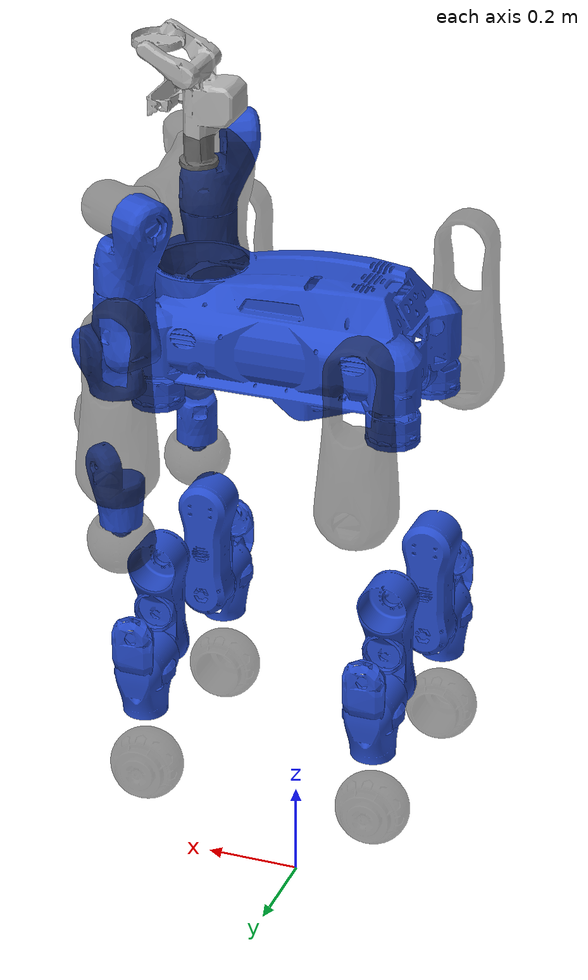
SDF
<sdf version='1.6'>
  <model name='centauro'>
    <link name='pelvis'>
      <pose frame=''>0 0 0 0 -0 0</pose>
      <inertial>
        <pose frame=''>-0.001632 0.002653 0.079167 0 -0 0</pose>
        <mass>26.5845</mass>
        <inertia>
          <ixx>0.391955</ixx>
          <ixy>0.0247813</ixy>
          <ixz>0.0171086</ixz>
          <iyy>1.00007</iyy>
          <iyz>0.00526271</iyz>
          <izz>1.068</izz>
        </inertia>
      </inertial>
      <collision name='pelvis_collision'>
        <pose frame=''>0 0 0 0 -0 0</pose>
        <geometry>
          <mesh>
            <scale>0.001 0.001 0.001</scale>
            <uri>model://centauro_urdf/meshes/simple/pelvis.stl</uri>
          </mesh>
        </geometry>
        <surface>
          <contact>
            <ode/>
          </contact>
          <friction>
            <ode/>
          </friction>
        </surface>
      </collision>
      <visual name='pelvis_visual'>
        <pose frame=''>0 0 0 0 -0 0</pose>
        <geometry>
          <mesh>
            <scale>0.001 0.001 0.001</scale>
            <uri>model://centauro_urdf/meshes/v2/pelvis.stl</uri>
          </mesh>
        </geometry>
        <material>
          <script>
            <name>Gazebo/LightBlueLaser</name>
            <uri>file://media/materials/scripts/gazebo.material</uri>
          </script>
        </material>
      </visual>
      <velocity_decay/>
      <gravity>1</gravity>
      <velocity_decay/>
      <sensor name='imu_link' type='imu'>
        <always_on>1</always_on>
        <update_rate>500</update_rate>
        <visualize>1</visualize>
        <topic>__default_topic__</topic>
        <imu>
          <angular_velocity/>
          <linear_acceleration/>
        </imu>
        <pose frame=''>0.248316 0 0.015 0 -0 0</pose>
      </sensor>
    </link>
    <link name='hip1_1'>
      <pose frame=''>0.25 0.125 -0.0566 0 -0 0</pose>
      <inertial>
        <pose frame=''>0.00036 0.033339 -0.05919 0 -0 0</pose>
        <mass>2.33492</mass>
        <inertia>
          <ixx>0.00684054</ixx>
          <ixy>1.85726e-05</ixy>
          <ixz>-4.8326e-05</ixz>
          <iyy>0.00262618</iyy>
          <iyz>0.000156427</iyz>
          <izz>0.00669334</izz>
        </inertia>
      </inertial>
      <collision name='hip1_1_collision'>
        <pose frame=''>0 0 0 0 -0 0</pose>
        <geometry>
          <mesh>
            <scale>0.001 -0.001 0.001</scale>
            <uri>model://centauro_urdf/meshes/v2/collision/hip-yaw.stl</uri>
          </mesh>
        </geometry>
        <surface>
          <contact>
            <ode/>
          </contact>
          <friction>
            <ode/>
          </friction>
        </surface>
      </collision>
      <visual name='hip1_1_visual'>
        <pose frame=''>0 0 0 0 -0 0</pose>
        <geometry>
          <mesh>
            <scale>0.001 -0.001 0.001</scale>
            <uri>model://centauro_urdf/meshes/v2/hip-yaw.stl</uri>
          </mesh>
        </geometry>
        <material>
          <script>
            <name>Gazebo/LightBlueLaser</name>
            <uri>file://media/materials/scripts/gazebo.material</uri>
          </script>
        </material>
      </visual>
      <gravity>1</gravity>
      <velocity_decay/>
    </link>
    <joint name='hip_yaw_1' type='revolute'>
      <child>hip1_1</child>
      <parent>pelvis</parent>
      <axis>
        <xyz>0 0 -1</xyz>
        <limit>
          <lower>-2.03</lower>
          <upper>2.51</upper>
          <effort>304</effort>
          <velocity>8.8</velocity>
        </limit>
        <dynamics>
          <spring_reference>0</spring_reference>
          <spring_stiffness>0</spring_stiffness>
        </dynamics>
        <use_parent_model_frame>1</use_parent_model_frame>
      </axis>
      <physics>
        <provide_feedback>1</provide_feedback>
        <ode>
          <provide_feedback>1</provide_feedback>
          <implicit_spring_damper>1</implicit_spring_damper>
          <cfm_damping>1</cfm_damping>
          <limit>
            <cfm>0</cfm>
            <erp>0.2</erp>
          </limit>
        </ode>
      </physics>
    </joint>
    <link name='hip2_1'>
      <pose frame=''>0.25 0.2396 -0.1191 1.5708 -0 0</pose>
      <inertial>
        <pose frame=''>-5e-06 -0.221402 0.033167 0 -0 0</pose>
        <mass>3.45721</mass>
        <inertia>
          <ixx>0.0504699</ixx>
          <ixy>-7.78494e-06</ixy>
          <ixz>-9.22058e-06</ixz>
          <iyy>0.0081816</iyy>
          <iyz>0.00597968</iyz>
          <izz>0.0482138</izz>
        </inertia>
      </inertial>
      <collision name='hip2_1_collision'>
        <pose frame=''>0 0 0 0 -0 0</pose>
        <geometry>
          <mesh>
            <scale>0.001 0.001 -0.001</scale>
            <uri>model://centauro_urdf/meshes/v2/collision/hip-pitch.stl</uri>
          </mesh>
        </geometry>
        <surface>
          <contact>
            <ode/>
          </contact>
          <friction>
            <ode/>
          </friction>
        </surface>
      </collision>
      <visual name='hip2_1_visual'>
        <pose frame=''>0 0 0 0 -0 0</pose>
        <geometry>
          <mesh>
            <scale>0.001 0.001 -0.001</scale>
            <uri>model://centauro_urdf/meshes/v2/hip-pitch.stl</uri>
          </mesh>
        </geometry>
        <material>
          <script>
            <name>Gazebo/BlackTransparent</name>
            <uri>file://media/materials/scripts/gazebo.material</uri>
          </script>
        </material>
      </visual>
      <gravity>1</gravity>
      <velocity_decay/>
    </link>
    <joint name='hip_pitch_1' type='revolute'>
      <child>hip2_1</child>
      <parent>hip1_1</parent>
      <axis>
        <xyz>0 1 -0</xyz>
        <limit>
          <lower>-2.0226</lower>
          <upper>2.02748</upper>
          <effort>304</effort>
          <velocity>8.8</velocity>
        </limit>
        <dynamics>
          <spring_reference>0</spring_reference>
          <spring_stiffness>0</spring_stiffness>
        </dynamics>
        <use_parent_model_frame>1</use_parent_model_frame>
      </axis>
      <physics>
        <provide_feedback>1</provide_feedback>
        <ode>
          <provide_feedback>1</provide_feedback>
          <implicit_spring_damper>1</implicit_spring_damper>
          <cfm_damping>1</cfm_damping>
          <limit>
            <cfm>0</cfm>
            <erp>0.2</erp>
          </limit>
        </ode>
      </physics>
    </joint>
    <link name='knee_1'>
      <pose frame=''>0.25 0.1214 -0.4191 -1.5708 -0 0</pose>
      <inertial>
        <pose frame=''>0.000121 0.146207 0.029741 0 -0 0</pose>
        <mass>2.11993</mass>
        <inertia>
          <ixx>0.0184264</ixx>
          <ixy>2.82266e-05</ixy>
          <ixz>-2.92043e-05</ixz>
          <iyy>0.00476856</iyy>
          <iyz>-0.00264077</iyz>
          <izz>0.0177937</izz>
        </inertia>
      </inertial>
      <collision name='knee_1_collision'>
        <pose frame=''>0 0 0 0 -0 0</pose>
        <geometry>
          <mesh>
            <scale>0.001 0.001 -0.001</scale>
            <uri>model://centauro_urdf/meshes/v2/collision/knee.stl</uri>
          </mesh>
        </geometry>
        <surface>
          <contact>
            <ode/>
          </contact>
          <friction>
            <ode/>
          </friction>
        </surface>
      </collision>
      <visual name='knee_1_visual'>
        <pose frame=''>0 0 0 0 -0 0</pose>
        <geometry>
          <mesh>
            <scale>0.001 0.001 -0.001</scale>
            <uri>model://centauro_urdf/meshes/v2/knee.stl</uri>
          </mesh>
        </geometry>
        <material>
          <script>
            <name>Gazebo/LightBlueLaser</name>
            <uri>file://media/materials/scripts/gazebo.material</uri>
          </script>
        </material>
      </visual>
      <gravity>1</gravity>
      <velocity_decay/>
    </link>
    <joint name='knee_pitch_1' type='revolute'>
      <child>knee_1</child>
      <parent>hip2_1</parent>
      <axis>
        <xyz>0 -1 0</xyz>
        <limit>
          <lower>-2.4056</lower>
          <upper>2.3994</upper>
          <effort>304</effort>
          <velocity>8.8</velocity>
        </limit>
        <dynamics>
          <spring_reference>0</spring_reference>
          <spring_stiffness>0</spring_stiffness>
        </dynamics>
        <use_parent_model_frame>1</use_parent_model_frame>
      </axis>
      <physics>
        <provide_feedback>1</provide_feedback>
        <ode>
          <provide_feedback>1</provide_feedback>
          <implicit_spring_damper>1</implicit_spring_damper>
          <cfm_damping>1</cfm_damping>
          <limit>
            <cfm>0</cfm>
            <erp>0.2</erp>
          </limit>
        </ode>
      </physics>
    </joint>
    <link name='ankle1_1'>
      <pose frame=''>0.25 0.22155 -0.6191 1.5708 -0 0</pose>
      <inertial>
        <pose frame=''>0.000124 -0.062747 -0.004907 0 -0 0</pose>
        <mass>1.40234</mass>
        <inertia>
          <ixx>0.00499288</ixx>
          <ixy>5.76236e-06</ixy>
          <ixz>1.96064e-05</ixz>
          <iyy>0.00176215</iyy>
          <iyz>0.000453151</iyz>
          <izz>0.00487063</izz>
        </inertia>
      </inertial>
      <collision name='ankle1_1_collision'>
        <pose frame=''>0 0 0 0 -0 0</pose>
        <geometry>
          <mesh>
            <scale>0.001 0.001 -0.001</scale>
            <uri>model://centauro_urdf/meshes/v2/collision/ankle-pitch.stl</uri>
          </mesh>
        </geometry>
        <surface>
          <contact>
            <ode/>
          </contact>
          <friction>
            <ode/>
          </friction>
        </surface>
      </collision>
      <visual name='ankle1_1_visual'>
        <pose frame=''>0 0 0 0 -0 0</pose>
        <geometry>
          <mesh>
            <scale>0.001 0.001 -0.001</scale>
            <uri>model://centauro_urdf/meshes/v2/ankle-pitch.stl</uri>
          </mesh>
        </geometry>
        <material>
          <script>
            <name>Gazebo/LightBlueLaser</name>
            <uri>file://media/materials/scripts/gazebo.material</uri>
          </script>
        </material>
      </visual>
      <gravity>1</gravity>
      <velocity_decay/>
    </link>
    <joint name='ankle_pitch_1' type='revolute'>
      <child>ankle1_1</child>
      <parent>knee_1</parent>
      <axis>
        <xyz>0 1 -0</xyz>
        <limit>
          <lower>-2.4056</lower>
          <upper>2.3184</upper>
          <effort>147</effort>
          <velocity>8.1</velocity>
        </limit>
        <dynamics>
          <spring_reference>0</spring_reference>
          <spring_stiffness>0</spring_stiffness>
        </dynamics>
        <use_parent_model_frame>1</use_parent_model_frame>
      </axis>
      <physics>
        <provide_feedback>1</provide_feedback>
        <ode>
          <provide_feedback>1</provide_feedback>
          <implicit_spring_damper>1</implicit_spring_damper>
          <cfm_damping>1</cfm_damping>
          <limit>
            <cfm>0</cfm>
            <erp>0.2</erp>
          </limit>
        </ode>
      </physics>
    </joint>
    <link name='ankle2_1'>
      <pose frame=''>0.25 0.2224 -0.7581 0 -0 0</pose>
      <inertial>
        <pose frame=''>0.00185 -0.000513 -0.067309 0 -0 0</pose>
        <mass>1.76567</mass>
        <inertia>
          <ixx>0.00739763</ixx>
          <ixy>9.75577e-07</ixy>
          <ixz>-0.000229525</ixz>
          <iyy>0.00544344</iyy>
          <iyz>3.63378e-05</iyz>
          <izz>0.00430551</izz>
        </inertia>
      </inertial>
      <collision name='ankle2_1_collision'>
        <pose frame=''>0 0 0 0 -0 0</pose>
        <geometry>
          <mesh>
            <scale>0.001 -0.001 0.001</scale>
            <uri>model://centauro_urdf/meshes/v2/collision/ankle-yaw.stl</uri>
          </mesh>
        </geometry>
        <surface>
          <contact>
            <ode/>
          </contact>
          <friction>
            <ode/>
          </friction>
        </surface>
      </collision>
      <visual name='ankle2_1_visual'>
        <pose frame=''>0 0 0 0 -0 0</pose>
        <geometry>
          <mesh>
            <scale>0.001 -0.001 0.001</scale>
            <uri>model://centauro_urdf/meshes/v2/ankle-yaw.stl</uri>
          </mesh>
        </geometry>
        <material>
          <script>
            <name>Gazebo/LightBlueLaser</name>
            <uri>file://media/materials/scripts/gazebo.material</uri>
          </script>
        </material>
      </visual>
      <gravity>1</gravity>
      <velocity_decay/>
    </link>
    <joint name='ankle_yaw_1' type='revolute'>
      <child>ankle2_1</child>
      <parent>ankle1_1</parent>
      <axis>
        <xyz>0 0 -1</xyz>
        <limit>
          <lower>-2.5626</lower>
          <upper>2.5384</upper>
          <effort>35</effort>
          <velocity>20</velocity>
        </limit>
        <dynamics>
          <spring_reference>0</spring_reference>
          <spring_stiffness>0</spring_stiffness>
        </dynamics>
        <use_parent_model_frame>1</use_parent_model_frame>
      </axis>
      <physics>
        <provide_feedback>1</provide_feedback>
        <ode>
          <provide_feedback>1</provide_feedback>
          <implicit_spring_damper>1</implicit_spring_damper>
          <cfm_damping>1</cfm_damping>
          <limit>
            <cfm>0</cfm>
            <erp>0.2</erp>
          </limit>
        </ode>
      </physics>
    </joint>
    <link name='wheel_1'>
      <pose frame=''>0.25 0.2224 -0.85645 1.5708 -0 0</pose>
      <inertial>
        <pose frame=''>0 0 -0.003116 0 -0 0</pose>
        <mass>1.11164</mass>
        <inertia>
          <ixx>0.00281741</ixx>
          <ixy>0</ixy>
          <ixz>-0</ixz>
          <iyy>0.00281756</iyy>
          <iyz>-0</iyz>
          <izz>0.00418172</izz>
        </inertia>
      </inertial>
      <collision name='wheel_1_collision'>
        <pose frame=''>0 0 0 0 -0 0</pose>
        <geometry>
          <cylinder>
            <length>0.11</length>
            <radius>0.078</radius>
          </cylinder>
        </geometry>
        <surface>
          <friction>
            <ode>
              <mu>0.5</mu>
              <mu2>0.5</mu2>
            </ode>
            <bullet>
              <friction>0.5</friction>
              <friction2>0.5</friction2>
            </bullet>
          </friction>
          <contact>
            <ode>
              <kp>2.1e+06</kp>
              <kd>1</kd>
              <max_vel>100</max_vel>
            </ode>
            <bullet>
              <soft_cfm>0.007</soft_cfm>
              <soft_erp>0.25</soft_erp>
              <kp>1e+06</kp>
              <kd>5</kd>
              <split_impulse>1</split_impulse>
              <split_impulse_penetration_threshold>-0.01</split_impulse_penetration_threshold>
            </bullet>
          </contact>
        </surface>
      </collision>
      <visual name='wheel_1_visual'>
        <pose frame=''>0 0 0 0 -0 0</pose>
        <geometry>
          <mesh>
            <scale>0.001 0.001 -0.001</scale>
            <uri>model://centauro_urdf/meshes/v2/wheel.stl</uri>
          </mesh>
        </geometry>
        <material>
          <script>
            <name>Gazebo/BlackTransparent</name>
            <uri>file://media/materials/scripts/gazebo.material</uri>
          </script>
        </material>
      </visual>
      <velocity_decay/>
      <gravity>1</gravity>
      <velocity_decay/>
    </link>
    <joint name='j_wheel_1' type='revolute'>
      <child>wheel_1</child>
      <parent>ankle2_1</parent>
      <axis>
        <xyz>0 1 -0</xyz>
        <limit>
          <lower>-1e+16</lower>
          <upper>1e+16</upper>
        </limit>
        <dynamics>
          <spring_reference>0</spring_reference>
          <spring_stiffness>0</spring_stiffness>
        </dynamics>
        <use_parent_model_frame>1</use_parent_model_frame>
      </axis>
      <physics>
        <provide_feedback>1</provide_feedback>
        <ode>
          <provide_feedback>1</provide_feedback>
          <implicit_spring_damper>1</implicit_spring_damper>
          <cfm_damping>1</cfm_damping>
          <limit>
            <cfm>0</cfm>
            <erp>0.2</erp>
          </limit>
        </ode>
      </physics>
    </joint>
    <link name='hip1_2'>
      <pose frame=''>0.25 -0.125 -0.0566 0 -0 0</pose>
      <inertial>
        <pose frame=''>0.00036 -0.033339 -0.05919 0 -0 0</pose>
        <mass>2.33492</mass>
        <inertia>
          <ixx>0.00684054</ixx>
          <ixy>-1.85726e-05</ixy>
          <ixz>-4.8326e-05</ixz>
          <iyy>0.00262618</iyy>
          <iyz>-0.000156427</iyz>
          <izz>0.00669334</izz>
        </inertia>
      </inertial>
      <collision name='hip1_2_collision'>
        <pose frame=''>0 0 0 0 -0 0</pose>
        <geometry>
          <mesh>
            <scale>0.001 0.001 0.001</scale>
            <uri>model://centauro_urdf/meshes/v2/collision/hip-yaw.stl</uri>
          </mesh>
        </geometry>
        <surface>
          <contact>
            <ode/>
          </contact>
          <friction>
            <ode/>
          </friction>
        </surface>
      </collision>
      <visual name='hip1_2_visual'>
        <pose frame=''>0 0 0 0 -0 0</pose>
        <geometry>
          <mesh>
            <scale>0.001 0.001 0.001</scale>
            <uri>model://centauro_urdf/meshes/v2/hip-yaw.stl</uri>
          </mesh>
        </geometry>
        <material>
          <script>
            <name>Gazebo/LightBlueLaser</name>
            <uri>file://media/materials/scripts/gazebo.material</uri>
          </script>
        </material>
      </visual>
      <gravity>1</gravity>
      <velocity_decay/>
    </link>
    <joint name='hip_yaw_2' type='revolute'>
      <child>hip1_2</child>
      <parent>pelvis</parent>
      <axis>
        <xyz>0 0 -1</xyz>
        <limit>
          <lower>-2.51</lower>
          <upper>2.03</upper>
          <effort>304</effort>
          <velocity>8.8</velocity>
        </limit>
        <dynamics>
          <spring_reference>0</spring_reference>
          <spring_stiffness>0</spring_stiffness>
        </dynamics>
        <use_parent_model_frame>1</use_parent_model_frame>
      </axis>
      <physics>
        <provide_feedback>1</provide_feedback>
        <ode>
          <provide_feedback>1</provide_feedback>
          <implicit_spring_damper>1</implicit_spring_damper>
          <cfm_damping>1</cfm_damping>
          <limit>
            <cfm>0</cfm>
            <erp>0.2</erp>
          </limit>
        </ode>
      </physics>
    </joint>
    <link name='hip2_2'>
      <pose frame=''>0.25 -0.2396 -0.1191 1.5708 -0 0</pose>
      <inertial>
        <pose frame=''>-5e-06 -0.221402 -0.033167 0 -0 0</pose>
        <mass>3.45721</mass>
        <inertia>
          <ixx>0.0504699</ixx>
          <ixy>-7.78494e-06</ixy>
          <ixz>9.22058e-06</ixz>
          <iyy>0.0081816</iyy>
          <iyz>-0.00597968</iyz>
          <izz>0.0482138</izz>
        </inertia>
      </inertial>
      <collision name='hip2_2_collision'>
        <pose frame=''>0 0 0 0 -0 0</pose>
        <geometry>
          <mesh>
            <scale>0.001 0.001 0.001</scale>
            <uri>model://centauro_urdf/meshes/v2/collision/hip-pitch.stl</uri>
          </mesh>
        </geometry>
        <surface>
          <contact>
            <ode/>
          </contact>
          <friction>
            <ode/>
          </friction>
        </surface>
      </collision>
      <visual name='hip2_2_visual'>
        <pose frame=''>0 0 0 0 -0 0</pose>
        <geometry>
          <mesh>
            <scale>0.001 0.001 0.001</scale>
            <uri>model://centauro_urdf/meshes/v2/hip-pitch.stl</uri>
          </mesh>
        </geometry>
        <material>
          <script>
            <name>Gazebo/BlackTransparent</name>
            <uri>file://media/materials/scripts/gazebo.material</uri>
          </script>
        </material>
      </visual>
      <gravity>1</gravity>
      <velocity_decay/>
    </link>
    <joint name='hip_pitch_2' type='revolute'>
      <child>hip2_2</child>
      <parent>hip1_2</parent>
      <axis>
        <xyz>0 -1 0</xyz>
        <limit>
          <lower>-2.0156</lower>
          <upper>2.0354</upper>
          <effort>304</effort>
          <velocity>8.8</velocity>
        </limit>
        <dynamics>
          <spring_reference>0</spring_reference>
          <spring_stiffness>0</spring_stiffness>
        </dynamics>
        <use_parent_model_frame>1</use_parent_model_frame>
      </axis>
      <physics>
        <provide_feedback>1</provide_feedback>
        <ode>
          <provide_feedback>1</provide_feedback>
          <implicit_spring_damper>1</implicit_spring_damper>
          <cfm_damping>1</cfm_damping>
          <limit>
            <cfm>0</cfm>
            <erp>0.2</erp>
          </limit>
        </ode>
      </physics>
    </joint>
    <link name='knee_2'>
      <pose frame=''>0.25 -0.1214 -0.4191 -1.5708 -0 0</pose>
      <inertial>
        <pose frame=''>0.000121 0.146207 -0.029741 0 -0 0</pose>
        <mass>2.11993</mass>
        <inertia>
          <ixx>0.0184264</ixx>
          <ixy>2.82266e-05</ixy>
          <ixz>2.92043e-05</ixz>
          <iyy>0.00476856</iyy>
          <iyz>0.00264077</iyz>
          <izz>0.0177937</izz>
        </inertia>
      </inertial>
      <collision name='knee_2_collision'>
        <pose frame=''>0 0 0 0 -0 0</pose>
        <geometry>
          <mesh>
            <scale>0.001 0.001 0.001</scale>
            <uri>model://centauro_urdf/meshes/v2/collision/knee.stl</uri>
          </mesh>
        </geometry>
        <surface>
          <contact>
            <ode/>
          </contact>
          <friction>
            <ode/>
          </friction>
        </surface>
      </collision>
      <visual name='knee_2_visual'>
        <pose frame=''>0 0 0 0 -0 0</pose>
        <geometry>
          <mesh>
            <scale>0.001 0.001 0.001</scale>
            <uri>model://centauro_urdf/meshes/v2/knee.stl</uri>
          </mesh>
        </geometry>
        <material>
          <script>
            <name>Gazebo/LightBlueLaser</name>
            <uri>file://media/materials/scripts/gazebo.material</uri>
          </script>
        </material>
      </visual>
      <gravity>1</gravity>
      <velocity_decay/>
    </link>
    <joint name='knee_pitch_2' type='revolute'>
      <child>knee_2</child>
      <parent>hip2_2</parent>
      <axis>
        <xyz>0 1 -0</xyz>
        <limit>
          <lower>-2.4006</lower>
          <upper>2.4034</upper>
          <effort>304</effort>
          <velocity>8.8</velocity>
        </limit>
        <dynamics>
          <spring_reference>0</spring_reference>
          <spring_stiffness>0</spring_stiffness>
        </dynamics>
        <use_parent_model_frame>1</use_parent_model_frame>
      </axis>
      <physics>
        <provide_feedback>1</provide_feedback>
        <ode>
          <provide_feedback>1</provide_feedback>
          <implicit_spring_damper>1</implicit_spring_damper>
          <cfm_damping>1</cfm_damping>
          <limit>
            <cfm>0</cfm>
            <erp>0.2</erp>
          </limit>
        </ode>
      </physics>
    </joint>
    <link name='ankle1_2'>
      <pose frame=''>0.25 -0.22155 -0.6191 1.5708 -0 0</pose>
      <inertial>
        <pose frame=''>0.000124 -0.062747 0.004907 0 -0 0</pose>
        <mass>1.40234</mass>
        <inertia>
          <ixx>0.00499288</ixx>
          <ixy>5.76236e-06</ixy>
          <ixz>-1.96064e-05</ixz>
          <iyy>0.00176215</iyy>
          <iyz>-0.000453151</iyz>
          <izz>0.00487063</izz>
        </inertia>
      </inertial>
      <collision name='ankle1_2_collision'>
        <pose frame=''>0 0 0 0 -0 0</pose>
        <geometry>
          <mesh>
            <scale>0.001 0.001 0.001</scale>
            <uri>model://centauro_urdf/meshes/v2/collision/ankle-pitch.stl</uri>
          </mesh>
        </geometry>
        <surface>
          <contact>
            <ode/>
          </contact>
          <friction>
            <ode/>
          </friction>
        </surface>
      </collision>
      <visual name='ankle1_2_visual'>
        <pose frame=''>0 0 0 0 -0 0</pose>
        <geometry>
          <mesh>
            <scale>0.001 0.001 0.001</scale>
            <uri>model://centauro_urdf/meshes/v2/ankle-pitch.stl</uri>
          </mesh>
        </geometry>
        <material>
          <script>
            <name>Gazebo/LightBlueLaser</name>
            <uri>file://media/materials/scripts/gazebo.material</uri>
          </script>
        </material>
      </visual>
      <gravity>1</gravity>
      <velocity_decay/>
    </link>
    <joint name='ankle_pitch_2' type='revolute'>
      <child>ankle1_2</child>
      <parent>knee_2</parent>
      <axis>
        <xyz>-0 -1 0</xyz>
        <limit>
          <lower>-2.3266</lower>
          <upper>2.3914</upper>
          <effort>147</effort>
          <velocity>8.1</velocity>
        </limit>
        <dynamics>
          <spring_reference>0</spring_reference>
          <spring_stiffness>0</spring_stiffness>
        </dynamics>
        <use_parent_model_frame>1</use_parent_model_frame>
      </axis>
      <physics>
        <provide_feedback>1</provide_feedback>
        <ode>
          <provide_feedback>1</provide_feedback>
          <implicit_spring_damper>1</implicit_spring_damper>
          <cfm_damping>1</cfm_damping>
          <limit>
            <cfm>0</cfm>
            <erp>0.2</erp>
          </limit>
        </ode>
      </physics>
    </joint>
    <link name='ankle2_2'>
      <pose frame=''>0.25 -0.2224 -0.7581 0 -0 0</pose>
      <inertial>
        <pose frame=''>0.00185 0.000513 -0.067309 0 -0 0</pose>
        <mass>1.76567</mass>
        <inertia>
          <ixx>0.00739763</ixx>
          <ixy>-9.75577e-07</ixy>
          <ixz>-0.000229525</ixz>
          <iyy>0.00544344</iyy>
          <iyz>-3.63378e-05</iyz>
          <izz>0.00430551</izz>
        </inertia>
      </inertial>
      <collision name='ankle2_2_collision'>
        <pose frame=''>0 0 0 0 -0 0</pose>
        <geometry>
          <mesh>
            <scale>0.001 0.001 0.001</scale>
            <uri>model://centauro_urdf/meshes/v2/collision/ankle-yaw.stl</uri>
          </mesh>
        </geometry>
        <surface>
          <contact>
            <ode/>
          </contact>
          <friction>
            <ode/>
          </friction>
        </surface>
      </collision>
      <visual name='ankle2_2_visual'>
        <pose frame=''>0 0 0 0 -0 0</pose>
        <geometry>
          <mesh>
            <scale>0.001 0.001 0.001</scale>
            <uri>model://centauro_urdf/meshes/v2/ankle-yaw.stl</uri>
          </mesh>
        </geometry>
        <material>
          <script>
            <name>Gazebo/LightBlueLaser</name>
            <uri>file://media/materials/scripts/gazebo.material</uri>
          </script>
        </material>
      </visual>
      <gravity>1</gravity>
      <velocity_decay/>
    </link>
    <joint name='ankle_yaw_2' type='revolute'>
      <child>ankle2_2</child>
      <parent>ankle1_2</parent>
      <axis>
        <xyz>0 0 -1</xyz>
        <limit>
          <lower>-2.5546</lower>
          <upper>2.5484</upper>
          <effort>35</effort>
          <velocity>20</velocity>
        </limit>
        <dynamics>
          <spring_reference>0</spring_reference>
          <spring_stiffness>0</spring_stiffness>
        </dynamics>
        <use_parent_model_frame>1</use_parent_model_frame>
      </axis>
      <physics>
        <provide_feedback>1</provide_feedback>
        <ode>
          <provide_feedback>1</provide_feedback>
          <implicit_spring_damper>1</implicit_spring_damper>
          <cfm_damping>1</cfm_damping>
          <limit>
            <cfm>0</cfm>
            <erp>0.2</erp>
          </limit>
        </ode>
      </physics>
    </joint>
    <link name='wheel_2'>
      <pose frame=''>0.25 -0.2224 -0.85645 1.5708 -0 0</pose>
      <inertial>
        <pose frame=''>0 0 0.003116 0 -0 0</pose>
        <mass>1.11164</mass>
        <inertia>
          <ixx>0.00281741</ixx>
          <ixy>0</ixy>
          <ixz>0</ixz>
          <iyy>0.00281756</iyy>
          <iyz>0</iyz>
          <izz>0.00418172</izz>
        </inertia>
      </inertial>
      <collision name='wheel_2_collision'>
        <pose frame=''>0 0 0 0 -0 0</pose>
        <geometry>
          <cylinder>
            <length>0.11</length>
            <radius>0.078</radius>
          </cylinder>
        </geometry>
        <surface>
          <friction>
            <ode>
              <mu>0.5</mu>
              <mu2>0.5</mu2>
            </ode>
            <bullet>
              <friction>0.5</friction>
              <friction2>0.5</friction2>
            </bullet>
          </friction>
          <contact>
            <ode>
              <kp>2.1e+06</kp>
              <kd>1</kd>
              <max_vel>100</max_vel>
            </ode>
            <bullet>
              <soft_cfm>0.007</soft_cfm>
              <soft_erp>0.25</soft_erp>
              <kp>1e+06</kp>
              <kd>5</kd>
              <split_impulse>1</split_impulse>
              <split_impulse_penetration_threshold>-0.01</split_impulse_penetration_threshold>
            </bullet>
          </contact>
        </surface>
      </collision>
      <visual name='wheel_2_visual'>
        <pose frame=''>0 0 0 0 -0 0</pose>
        <geometry>
          <mesh>
            <scale>0.001 0.001 0.001</scale>
            <uri>model://centauro_urdf/meshes/v2/wheel.stl</uri>
          </mesh>
        </geometry>
        <material>
          <script>
            <name>Gazebo/BlackTransparent</name>
            <uri>file://media/materials/scripts/gazebo.material</uri>
          </script>
        </material>
      </visual>
      <velocity_decay/>
      <gravity>1</gravity>
      <velocity_decay/>
    </link>
    <joint name='j_wheel_2' type='revolute'>
      <child>wheel_2</child>
      <parent>ankle2_2</parent>
      <axis>
        <xyz>-0 -1 0</xyz>
        <limit>
          <lower>-1e+16</lower>
          <upper>1e+16</upper>
        </limit>
        <dynamics>
          <spring_reference>0</spring_reference>
          <spring_stiffness>0</spring_stiffness>
        </dynamics>
        <use_parent_model_frame>1</use_parent_model_frame>
      </axis>
      <physics>
        <provide_feedback>1</provide_feedback>
        <ode>
          <provide_feedback>1</provide_feedback>
          <implicit_spring_damper>1</implicit_spring_damper>
          <cfm_damping>1</cfm_damping>
          <limit>
            <cfm>0</cfm>
            <erp>0.2</erp>
          </limit>
        </ode>
      </physics>
    </joint>
    <link name='hip1_3'>
      <pose frame=''>-0.25 0.125 -0.0566 0 -0 0</pose>
      <inertial>
        <pose frame=''>0.00036 0.033339 -0.05919 0 -0 0</pose>
        <mass>2.33492</mass>
        <inertia>
          <ixx>0.00684054</ixx>
          <ixy>1.85726e-05</ixy>
          <ixz>-4.8326e-05</ixz>
          <iyy>0.00262618</iyy>
          <iyz>0.000156427</iyz>
          <izz>0.00669334</izz>
        </inertia>
      </inertial>
      <collision name='hip1_3_collision'>
        <pose frame=''>0 0 0 0 -0 0</pose>
        <geometry>
          <mesh>
            <scale>0.001 -0.001 0.001</scale>
            <uri>model://centauro_urdf/meshes/v2/collision/hip-yaw.stl</uri>
          </mesh>
        </geometry>
        <surface>
          <contact>
            <ode/>
          </contact>
          <friction>
            <ode/>
          </friction>
        </surface>
      </collision>
      <visual name='hip1_3_visual'>
        <pose frame=''>0 0 0 0 -0 0</pose>
        <geometry>
          <mesh>
            <scale>0.001 -0.001 0.001</scale>
            <uri>model://centauro_urdf/meshes/v2/hip-yaw.stl</uri>
          </mesh>
        </geometry>
        <material>
          <script>
            <name>Gazebo/LightBlueLaser</name>
            <uri>file://media/materials/scripts/gazebo.material</uri>
          </script>
        </material>
      </visual>
      <gravity>1</gravity>
      <velocity_decay/>
    </link>
    <joint name='hip_yaw_3' type='revolute'>
      <child>hip1_3</child>
      <parent>pelvis</parent>
      <axis>
        <xyz>0 0 -1</xyz>
        <limit>
          <lower>-2.51</lower>
          <upper>2.03</upper>
          <effort>304</effort>
          <velocity>8.8</velocity>
        </limit>
        <dynamics>
          <spring_reference>0</spring_reference>
          <spring_stiffness>0</spring_stiffness>
        </dynamics>
        <use_parent_model_frame>1</use_parent_model_frame>
      </axis>
      <physics>
        <provide_feedback>1</provide_feedback>
        <ode>
          <provide_feedback>1</provide_feedback>
          <implicit_spring_damper>1</implicit_spring_damper>
          <cfm_damping>1</cfm_damping>
          <limit>
            <cfm>0</cfm>
            <erp>0.2</erp>
          </limit>
        </ode>
      </physics>
    </joint>
    <link name='hip2_3'>
      <pose frame=''>-0.25 0.2396 -0.1191 1.5708 -0 0</pose>
      <inertial>
        <pose frame=''>-5e-06 -0.221402 0.033167 0 -0 0</pose>
        <mass>3.45721</mass>
        <inertia>
          <ixx>0.0504699</ixx>
          <ixy>-7.78494e-06</ixy>
          <ixz>-9.22058e-06</ixz>
          <iyy>0.0081816</iyy>
          <iyz>0.00597968</iyz>
          <izz>0.0482138</izz>
        </inertia>
      </inertial>
      <collision name='hip2_3_collision'>
        <pose frame=''>0 0 0 0 -0 0</pose>
        <geometry>
          <mesh>
            <scale>0.001 0.001 -0.001</scale>
            <uri>model://centauro_urdf/meshes/v2/collision/hip-pitch.stl</uri>
          </mesh>
        </geometry>
        <surface>
          <contact>
            <ode/>
          </contact>
          <friction>
            <ode/>
          </friction>
        </surface>
      </collision>
      <visual name='hip2_3_visual'>
        <pose frame=''>0 0 0 0 -0 0</pose>
        <geometry>
          <mesh>
            <scale>0.001 0.001 -0.001</scale>
            <uri>model://centauro_urdf/meshes/v2/hip-pitch.stl</uri>
          </mesh>
        </geometry>
        <material>
          <script>
            <name>Gazebo/BlackTransparent</name>
            <uri>file://media/materials/scripts/gazebo.material</uri>
          </script>
        </material>
      </visual>
      <gravity>1</gravity>
      <velocity_decay/>
    </link>
    <joint name='hip_pitch_3' type='revolute'>
      <child>hip2_3</child>
      <parent>hip1_3</parent>
      <axis>
        <xyz>0 1 -0</xyz>
        <limit>
          <lower>-2.0126</lower>
          <upper>2.0384</upper>
          <effort>304</effort>
          <velocity>8.8</velocity>
        </limit>
        <dynamics>
          <spring_reference>0</spring_reference>
          <spring_stiffness>0</spring_stiffness>
        </dynamics>
        <use_parent_model_frame>1</use_parent_model_frame>
      </axis>
      <physics>
        <provide_feedback>1</provide_feedback>
        <ode>
          <provide_feedback>1</provide_feedback>
          <implicit_spring_damper>1</implicit_spring_damper>
          <cfm_damping>1</cfm_damping>
          <limit>
            <cfm>0</cfm>
            <erp>0.2</erp>
          </limit>
        </ode>
      </physics>
    </joint>
    <link name='knee_3'>
      <pose frame=''>-0.25 0.1214 -0.4191 -1.5708 -0 0</pose>
      <inertial>
        <pose frame=''>0.000121 0.146207 0.029741 0 -0 0</pose>
        <mass>2.11993</mass>
        <inertia>
          <ixx>0.0184264</ixx>
          <ixy>2.82266e-05</ixy>
          <ixz>-2.92043e-05</ixz>
          <iyy>0.00476856</iyy>
          <iyz>-0.00264077</iyz>
          <izz>0.0177937</izz>
        </inertia>
      </inertial>
      <collision name='knee_3_collision'>
        <pose frame=''>0 0 0 0 -0 0</pose>
        <geometry>
          <mesh>
            <scale>0.001 0.001 -0.001</scale>
            <uri>model://centauro_urdf/meshes/v2/collision/knee.stl</uri>
          </mesh>
        </geometry>
        <surface>
          <contact>
            <ode/>
          </contact>
          <friction>
            <ode/>
          </friction>
        </surface>
      </collision>
      <visual name='knee_3_visual'>
        <pose frame=''>0 0 0 0 -0 0</pose>
        <geometry>
          <mesh>
            <scale>0.001 0.001 -0.001</scale>
            <uri>model://centauro_urdf/meshes/v2/knee.stl</uri>
          </mesh>
        </geometry>
        <material>
          <script>
            <name>Gazebo/LightBlueLaser</name>
            <uri>file://media/materials/scripts/gazebo.material</uri>
          </script>
        </material>
      </visual>
      <gravity>1</gravity>
      <velocity_decay/>
    </link>
    <joint name='knee_pitch_3' type='revolute'>
      <child>knee_3</child>
      <parent>hip2_3</parent>
      <axis>
        <xyz>0 -1 0</xyz>
        <limit>
          <lower>-2.4056</lower>
          <upper>2.4064</upper>
          <effort>304</effort>
          <velocity>8.8</velocity>
        </limit>
        <dynamics>
          <spring_reference>0</spring_reference>
          <spring_stiffness>0</spring_stiffness>
        </dynamics>
        <use_parent_model_frame>1</use_parent_model_frame>
      </axis>
      <physics>
        <provide_feedback>1</provide_feedback>
        <ode>
          <provide_feedback>1</provide_feedback>
          <implicit_spring_damper>1</implicit_spring_damper>
          <cfm_damping>1</cfm_damping>
          <limit>
            <cfm>0</cfm>
            <erp>0.2</erp>
          </limit>
        </ode>
      </physics>
    </joint>
    <link name='ankle1_3'>
      <pose frame=''>-0.25 0.22155 -0.6191 1.5708 -0 0</pose>
      <inertial>
        <pose frame=''>0.000124 -0.062747 -0.004907 0 -0 0</pose>
        <mass>1.40234</mass>
        <inertia>
          <ixx>0.00499288</ixx>
          <ixy>5.76236e-06</ixy>
          <ixz>1.96064e-05</ixz>
          <iyy>0.00176215</iyy>
          <iyz>0.000453151</iyz>
          <izz>0.00487063</izz>
        </inertia>
      </inertial>
      <collision name='ankle1_3_collision'>
        <pose frame=''>0 0 0 0 -0 0</pose>
        <geometry>
          <mesh>
            <scale>0.001 0.001 -0.001</scale>
            <uri>model://centauro_urdf/meshes/v2/collision/ankle-pitch.stl</uri>
          </mesh>
        </geometry>
        <surface>
          <contact>
            <ode/>
          </contact>
          <friction>
            <ode/>
          </friction>
        </surface>
      </collision>
      <visual name='ankle1_3_visual'>
        <pose frame=''>0 0 0 0 -0 0</pose>
        <geometry>
          <mesh>
            <scale>0.001 0.001 -0.001</scale>
            <uri>model://centauro_urdf/meshes/v2/ankle-pitch.stl</uri>
          </mesh>
        </geometry>
        <material>
          <script>
            <name>Gazebo/LightBlueLaser</name>
            <uri>file://media/materials/scripts/gazebo.material</uri>
          </script>
        </material>
      </visual>
      <gravity>1</gravity>
      <velocity_decay/>
    </link>
    <joint name='ankle_pitch_3' type='revolute'>
      <child>ankle1_3</child>
      <parent>knee_3</parent>
      <axis>
        <xyz>0 1 -0</xyz>
        <limit>
          <lower>-2.4696</lower>
          <upper>2.4464</upper>
          <effort>147</effort>
          <velocity>8.1</velocity>
        </limit>
        <dynamics>
          <spring_reference>0</spring_reference>
          <spring_stiffness>0</spring_stiffness>
        </dynamics>
        <use_parent_model_frame>1</use_parent_model_frame>
      </axis>
      <physics>
        <provide_feedback>1</provide_feedback>
        <ode>
          <provide_feedback>1</provide_feedback>
          <implicit_spring_damper>1</implicit_spring_damper>
          <cfm_damping>1</cfm_damping>
          <limit>
            <cfm>0</cfm>
            <erp>0.2</erp>
          </limit>
        </ode>
      </physics>
    </joint>
    <link name='ankle2_3'>
      <pose frame=''>-0.25 0.2224 -0.7581 0 -0 0</pose>
      <inertial>
        <pose frame=''>0.00185 -0.000513 -0.067309 0 -0 0</pose>
        <mass>1.76567</mass>
        <inertia>
          <ixx>0.00739763</ixx>
          <ixy>9.75577e-07</ixy>
          <ixz>-0.000229525</ixz>
          <iyy>0.00544344</iyy>
          <iyz>3.63378e-05</iyz>
          <izz>0.00430551</izz>
        </inertia>
      </inertial>
      <collision name='ankle2_3_collision'>
        <pose frame=''>0 0 0 0 -0 0</pose>
        <geometry>
          <mesh>
            <scale>0.001 -0.001 0.001</scale>
            <uri>model://centauro_urdf/meshes/v2/collision/ankle-yaw.stl</uri>
          </mesh>
        </geometry>
        <surface>
          <contact>
            <ode/>
          </contact>
          <friction>
            <ode/>
          </friction>
        </surface>
      </collision>
      <visual name='ankle2_3_visual'>
        <pose frame=''>0 0 0 0 -0 0</pose>
        <geometry>
          <mesh>
            <scale>0.001 -0.001 0.001</scale>
            <uri>model://centauro_urdf/meshes/v2/ankle-yaw.stl</uri>
          </mesh>
        </geometry>
        <material>
          <script>
            <name>Gazebo/LightBlueLaser</name>
            <uri>file://media/materials/scripts/gazebo.material</uri>
          </script>
        </material>
      </visual>
      <gravity>1</gravity>
      <velocity_decay/>
    </link>
    <joint name='ankle_yaw_3' type='revolute'>
      <child>ankle2_3</child>
      <parent>ankle1_3</parent>
      <axis>
        <xyz>0 0 -1</xyz>
        <limit>
          <lower>-2.5606</lower>
          <upper>2.5454</upper>
          <effort>35</effort>
          <velocity>20</velocity>
        </limit>
        <dynamics>
          <spring_reference>0</spring_reference>
          <spring_stiffness>0</spring_stiffness>
        </dynamics>
        <use_parent_model_frame>1</use_parent_model_frame>
      </axis>
      <physics>
        <provide_feedback>1</provide_feedback>
        <ode>
          <provide_feedback>1</provide_feedback>
          <implicit_spring_damper>1</implicit_spring_damper>
          <cfm_damping>1</cfm_damping>
          <limit>
            <cfm>0</cfm>
            <erp>0.2</erp>
          </limit>
        </ode>
      </physics>
    </joint>
    <link name='wheel_3'>
      <pose frame=''>-0.25 0.2224 -0.85645 1.5708 -0 0</pose>
      <inertial>
        <pose frame=''>0 0 -0.003116 0 -0 0</pose>
        <mass>1.11164</mass>
        <inertia>
          <ixx>0.00281741</ixx>
          <ixy>0</ixy>
          <ixz>-0</ixz>
          <iyy>0.00281756</iyy>
          <iyz>-0</iyz>
          <izz>0.00418172</izz>
        </inertia>
      </inertial>
      <collision name='wheel_3_collision'>
        <pose frame=''>0 0 0 0 -0 0</pose>
        <geometry>
          <cylinder>
            <length>0.11</length>
            <radius>0.078</radius>
          </cylinder>
        </geometry>
        <surface>
          <friction>
            <ode>
              <mu>0.5</mu>
              <mu2>0.5</mu2>
            </ode>
            <bullet>
              <friction>0.5</friction>
              <friction2>0.5</friction2>
            </bullet>
          </friction>
          <contact>
            <ode>
              <kp>2.1e+06</kp>
              <kd>1</kd>
              <max_vel>100</max_vel>
            </ode>
            <bullet>
              <soft_cfm>0.007</soft_cfm>
              <soft_erp>0.25</soft_erp>
              <kp>1e+06</kp>
              <kd>5</kd>
              <split_impulse>1</split_impulse>
              <split_impulse_penetration_threshold>-0.01</split_impulse_penetration_threshold>
            </bullet>
          </contact>
        </surface>
      </collision>
      <visual name='wheel_3_visual'>
        <pose frame=''>0 0 0 0 -0 0</pose>
        <geometry>
          <mesh>
            <scale>0.001 0.001 -0.001</scale>
            <uri>model://centauro_urdf/meshes/v2/wheel.stl</uri>
          </mesh>
        </geometry>
        <material>
          <script>
            <name>Gazebo/BlackTransparent</name>
            <uri>file://media/materials/scripts/gazebo.material</uri>
          </script>
        </material>
      </visual>
      <velocity_decay/>
      <gravity>1</gravity>
      <velocity_decay/>
    </link>
    <joint name='j_wheel_3' type='revolute'>
      <child>wheel_3</child>
      <parent>ankle2_3</parent>
      <axis>
        <xyz>0 1 -0</xyz>
        <limit>
          <lower>-1e+16</lower>
          <upper>1e+16</upper>
        </limit>
        <dynamics>
          <spring_reference>0</spring_reference>
          <spring_stiffness>0</spring_stiffness>
        </dynamics>
        <use_parent_model_frame>1</use_parent_model_frame>
      </axis>
      <physics>
        <provide_feedback>1</provide_feedback>
        <ode>
          <provide_feedback>1</provide_feedback>
          <implicit_spring_damper>1</implicit_spring_damper>
          <cfm_damping>1</cfm_damping>
          <limit>
            <cfm>0</cfm>
            <erp>0.2</erp>
          </limit>
        </ode>
      </physics>
    </joint>
    <link name='hip1_4'>
      <pose frame=''>-0.25 -0.125 -0.0566 0 -0 0</pose>
      <inertial>
        <pose frame=''>0.00036 -0.033339 -0.05919 0 -0 0</pose>
        <mass>2.33492</mass>
        <inertia>
          <ixx>0.00684054</ixx>
          <ixy>-1.85726e-05</ixy>
          <ixz>-4.8326e-05</ixz>
          <iyy>0.00262618</iyy>
          <iyz>-0.000156427</iyz>
          <izz>0.00669334</izz>
        </inertia>
      </inertial>
      <collision name='hip1_4_collision'>
        <pose frame=''>0 0 0 0 -0 0</pose>
        <geometry>
          <mesh>
            <scale>0.001 0.001 0.001</scale>
            <uri>model://centauro_urdf/meshes/v2/collision/hip-yaw.stl</uri>
          </mesh>
        </geometry>
        <surface>
          <contact>
            <ode/>
          </contact>
          <friction>
            <ode/>
          </friction>
        </surface>
      </collision>
      <visual name='hip1_4_visual'>
        <pose frame=''>0 0 0 0 -0 0</pose>
        <geometry>
          <mesh>
            <scale>0.001 0.001 0.001</scale>
            <uri>model://centauro_urdf/meshes/v2/hip-yaw.stl</uri>
          </mesh>
        </geometry>
        <material>
          <script>
            <name>Gazebo/LightBlueLaser</name>
            <uri>file://media/materials/scripts/gazebo.material</uri>
          </script>
        </material>
      </visual>
      <gravity>1</gravity>
      <velocity_decay/>
    </link>
    <joint name='hip_yaw_4' type='revolute'>
      <child>hip1_4</child>
      <parent>pelvis</parent>
      <axis>
        <xyz>0 0 -1</xyz>
        <limit>
          <lower>-2.03</lower>
          <upper>2.51</upper>
          <effort>304</effort>
          <velocity>8.8</velocity>
        </limit>
        <dynamics>
          <spring_reference>0</spring_reference>
          <spring_stiffness>0</spring_stiffness>
        </dynamics>
        <use_parent_model_frame>1</use_parent_model_frame>
      </axis>
      <physics>
        <provide_feedback>1</provide_feedback>
        <ode>
          <provide_feedback>1</provide_feedback>
          <implicit_spring_damper>1</implicit_spring_damper>
          <cfm_damping>1</cfm_damping>
          <limit>
            <cfm>0</cfm>
            <erp>0.2</erp>
          </limit>
        </ode>
      </physics>
    </joint>
    <link name='hip2_4'>
      <pose frame=''>-0.25 -0.2396 -0.1191 1.5708 -0 0</pose>
      <inertial>
        <pose frame=''>-5e-06 -0.221402 -0.033167 0 -0 0</pose>
        <mass>3.45721</mass>
        <inertia>
          <ixx>0.0504699</ixx>
          <ixy>-7.78494e-06</ixy>
          <ixz>9.22058e-06</ixz>
          <iyy>0.0081816</iyy>
          <iyz>-0.00597968</iyz>
          <izz>0.0482138</izz>
        </inertia>
      </inertial>
      <collision name='hip2_4_collision'>
        <pose frame=''>0 0 0 0 -0 0</pose>
        <geometry>
          <mesh>
            <scale>0.001 0.001 0.001</scale>
            <uri>model://centauro_urdf/meshes/v2/collision/hip-pitch.stl</uri>
          </mesh>
        </geometry>
        <surface>
          <contact>
            <ode/>
          </contact>
          <friction>
            <ode/>
          </friction>
        </surface>
      </collision>
      <visual name='hip2_4_visual'>
        <pose frame=''>0 0 0 0 -0 0</pose>
        <geometry>
          <mesh>
            <scale>0.001 0.001 0.001</scale>
            <uri>model://centauro_urdf/meshes/v2/hip-pitch.stl</uri>
          </mesh>
        </geometry>
        <material>
          <script>
            <name>Gazebo/BlackTransparent</name>
            <uri>file://media/materials/scripts/gazebo.material</uri>
          </script>
        </material>
      </visual>
      <gravity>1</gravity>
      <velocity_decay/>
    </link>
    <joint name='hip_pitch_4' type='revolute'>
      <child>hip2_4</child>
      <parent>hip1_4</parent>
      <axis>
        <xyz>0 -1 0</xyz>
        <limit>
          <lower>-2.0326</lower>
          <upper>2.0524</upper>
          <effort>304</effort>
          <velocity>8.8</velocity>
        </limit>
        <dynamics>
          <spring_reference>0</spring_reference>
          <spring_stiffness>0</spring_stiffness>
        </dynamics>
        <use_parent_model_frame>1</use_parent_model_frame>
      </axis>
      <physics>
        <provide_feedback>1</provide_feedback>
        <ode>
          <provide_feedback>1</provide_feedback>
          <implicit_spring_damper>1</implicit_spring_damper>
          <cfm_damping>1</cfm_damping>
          <limit>
            <cfm>0</cfm>
            <erp>0.2</erp>
          </limit>
        </ode>
      </physics>
    </joint>
    <link name='knee_4'>
      <pose frame=''>-0.25 -0.1214 -0.4191 -1.5708 -0 0</pose>
      <inertial>
        <pose frame=''>0.000121 0.146207 -0.029741 0 -0 0</pose>
        <mass>2.11993</mass>
        <inertia>
          <ixx>0.0184264</ixx>
          <ixy>2.82266e-05</ixy>
          <ixz>2.92043e-05</ixz>
          <iyy>0.00476856</iyy>
          <iyz>0.00264077</iyz>
          <izz>0.0177937</izz>
        </inertia>
      </inertial>
      <collision name='knee_4_collision'>
        <pose frame=''>0 0 0 0 -0 0</pose>
        <geometry>
          <mesh>
            <scale>0.001 0.001 0.001</scale>
            <uri>model://centauro_urdf/meshes/v2/collision/knee.stl</uri>
          </mesh>
        </geometry>
        <surface>
          <contact>
            <ode/>
          </contact>
          <friction>
            <ode/>
          </friction>
        </surface>
      </collision>
      <visual name='knee_4_visual'>
        <pose frame=''>0 0 0 0 -0 0</pose>
        <geometry>
          <mesh>
            <scale>0.001 0.001 0.001</scale>
            <uri>model://centauro_urdf/meshes/v2/knee.stl</uri>
          </mesh>
        </geometry>
        <material>
          <script>
            <name>Gazebo/LightBlueLaser</name>
            <uri>file://media/materials/scripts/gazebo.material</uri>
          </script>
        </material>
      </visual>
      <gravity>1</gravity>
      <velocity_decay/>
    </link>
    <joint name='knee_pitch_4' type='revolute'>
      <child>knee_4</child>
      <parent>hip2_4</parent>
      <axis>
        <xyz>0 1 -0</xyz>
        <limit>
          <lower>-2.4176</lower>
          <upper>2.3884</upper>
          <effort>304</effort>
          <velocity>8.8</velocity>
        </limit>
        <dynamics>
          <spring_reference>0</spring_reference>
          <spring_stiffness>0</spring_stiffness>
        </dynamics>
        <use_parent_model_frame>1</use_parent_model_frame>
      </axis>
      <physics>
        <provide_feedback>1</provide_feedback>
        <ode>
          <provide_feedback>1</provide_feedback>
          <implicit_spring_damper>1</implicit_spring_damper>
          <cfm_damping>1</cfm_damping>
          <limit>
            <cfm>0</cfm>
            <erp>0.2</erp>
          </limit>
        </ode>
      </physics>
    </joint>
    <link name='ankle1_4'>
      <pose frame=''>-0.25 -0.22155 -0.6191 1.5708 -0 0</pose>
      <inertial>
        <pose frame=''>0.000124 -0.062747 0.004907 0 -0 0</pose>
        <mass>1.40234</mass>
        <inertia>
          <ixx>0.00499288</ixx>
          <ixy>5.76236e-06</ixy>
          <ixz>-1.96064e-05</ixz>
          <iyy>0.00176215</iyy>
          <iyz>-0.000453151</iyz>
          <izz>0.00487063</izz>
        </inertia>
      </inertial>
      <collision name='ankle1_4_collision'>
        <pose frame=''>0 0 0 0 -0 0</pose>
        <geometry>
          <mesh>
            <scale>0.001 0.001 0.001</scale>
            <uri>model://centauro_urdf/meshes/v2/collision/ankle-pitch.stl</uri>
          </mesh>
        </geometry>
        <surface>
          <contact>
            <ode/>
          </contact>
          <friction>
            <ode/>
          </friction>
        </surface>
      </collision>
      <visual name='ankle1_4_visual'>
        <pose frame=''>0 0 0 0 -0 0</pose>
        <geometry>
          <mesh>
            <scale>0.001 0.001 0.001</scale>
            <uri>model://centauro_urdf/meshes/v2/ankle-pitch.stl</uri>
          </mesh>
        </geometry>
        <material>
          <script>
            <name>Gazebo/LightBlueLaser</name>
            <uri>file://media/materials/scripts/gazebo.material</uri>
          </script>
        </material>
      </visual>
      <gravity>1</gravity>
      <velocity_decay/>
    </link>
    <joint name='ankle_pitch_4' type='revolute'>
      <child>ankle1_4</child>
      <parent>knee_4</parent>
      <axis>
        <xyz>-0 -1 0</xyz>
        <limit>
          <lower>-2.3426</lower>
          <upper>2.3934</upper>
          <effort>147</effort>
          <velocity>8.1</velocity>
        </limit>
        <dynamics>
          <spring_reference>0</spring_reference>
          <spring_stiffness>0</spring_stiffness>
        </dynamics>
        <use_parent_model_frame>1</use_parent_model_frame>
      </axis>
      <physics>
        <provide_feedback>1</provide_feedback>
        <ode>
          <provide_feedback>1</provide_feedback>
          <implicit_spring_damper>1</implicit_spring_damper>
          <cfm_damping>1</cfm_damping>
          <limit>
            <cfm>0</cfm>
            <erp>0.2</erp>
          </limit>
        </ode>
      </physics>
    </joint>
    <link name='ankle2_4'>
      <pose frame=''>-0.25 -0.2224 -0.7581 0 -0 0</pose>
      <inertial>
        <pose frame=''>0.00185 0.000513 -0.067309 0 -0 0</pose>
        <mass>1.76567</mass>
        <inertia>
          <ixx>0.00739763</ixx>
          <ixy>-9.75577e-07</ixy>
          <ixz>-0.000229525</ixz>
          <iyy>0.00544344</iyy>
          <iyz>-3.63378e-05</iyz>
          <izz>0.00430551</izz>
        </inertia>
      </inertial>
      <collision name='ankle2_4_collision'>
        <pose frame=''>0 0 0 0 -0 0</pose>
        <geometry>
          <mesh>
            <scale>0.001 0.001 0.001</scale>
            <uri>model://centauro_urdf/meshes/v2/collision/ankle-yaw.stl</uri>
          </mesh>
        </geometry>
        <surface>
          <contact>
            <ode/>
          </contact>
          <friction>
            <ode/>
          </friction>
        </surface>
      </collision>
      <visual name='ankle2_4_visual'>
        <pose frame=''>0 0 0 0 -0 0</pose>
        <geometry>
          <mesh>
            <scale>0.001 0.001 0.001</scale>
            <uri>model://centauro_urdf/meshes/v2/ankle-yaw.stl</uri>
          </mesh>
        </geometry>
        <material>
          <script>
            <name>Gazebo/LightBlueLaser</name>
            <uri>file://media/materials/scripts/gazebo.material</uri>
          </script>
        </material>
      </visual>
      <gravity>1</gravity>
      <velocity_decay/>
    </link>
    <joint name='ankle_yaw_4' type='revolute'>
      <child>ankle2_4</child>
      <parent>ankle1_4</parent>
      <axis>
        <xyz>0 0 -1</xyz>
        <limit>
          <lower>-2.6046</lower>
          <upper>2.5514</upper>
          <effort>35</effort>
          <velocity>20</velocity>
        </limit>
        <dynamics>
          <spring_reference>0</spring_reference>
          <spring_stiffness>0</spring_stiffness>
        </dynamics>
        <use_parent_model_frame>1</use_parent_model_frame>
      </axis>
      <physics>
        <provide_feedback>1</provide_feedback>
        <ode>
          <provide_feedback>1</provide_feedback>
          <implicit_spring_damper>1</implicit_spring_damper>
          <cfm_damping>1</cfm_damping>
          <limit>
            <cfm>0</cfm>
            <erp>0.2</erp>
          </limit>
        </ode>
      </physics>
    </joint>
    <link name='wheel_4'>
      <pose frame=''>-0.25 -0.2224 -0.85645 1.5708 -0 0</pose>
      <inertial>
        <pose frame=''>0 0 0.003116 0 -0 0</pose>
        <mass>1.11164</mass>
        <inertia>
          <ixx>0.00281741</ixx>
          <ixy>0</ixy>
          <ixz>0</ixz>
          <iyy>0.00281756</iyy>
          <iyz>0</iyz>
          <izz>0.00418172</izz>
        </inertia>
      </inertial>
      <collision name='wheel_4_collision'>
        <pose frame=''>0 0 0 0 -0 0</pose>
        <geometry>
          <cylinder>
            <length>0.11</length>
            <radius>0.078</radius>
          </cylinder>
        </geometry>
        <surface>
          <friction>
            <ode>
              <mu>0.5</mu>
              <mu2>0.5</mu2>
            </ode>
            <bullet>
              <friction>0.5</friction>
              <friction2>0.5</friction2>
            </bullet>
          </friction>
          <contact>
            <ode>
              <kp>2.1e+06</kp>
              <kd>1</kd>
              <max_vel>100</max_vel>
            </ode>
            <bullet>
              <soft_cfm>0.007</soft_cfm>
              <soft_erp>0.25</soft_erp>
              <kp>1e+06</kp>
              <kd>5</kd>
              <split_impulse>1</split_impulse>
              <split_impulse_penetration_threshold>-0.01</split_impulse_penetration_threshold>
            </bullet>
          </contact>
        </surface>
      </collision>
      <visual name='wheel_4_visual'>
        <pose frame=''>0 0 0 0 -0 0</pose>
        <geometry>
          <mesh>
            <scale>0.001 0.001 0.001</scale>
            <uri>model://centauro_urdf/meshes/v2/wheel.stl</uri>
          </mesh>
        </geometry>
        <material>
          <script>
            <name>Gazebo/BlackTransparent</name>
            <uri>file://media/materials/scripts/gazebo.material</uri>
          </script>
        </material>
      </visual>
      <velocity_decay/>
      <gravity>1</gravity>
      <velocity_decay/>
    </link>
    <joint name='j_wheel_4' type='revolute'>
      <child>wheel_4</child>
      <parent>ankle2_4</parent>
      <axis>
        <xyz>-0 -1 0</xyz>
        <limit>
          <lower>-1e+16</lower>
          <upper>1e+16</upper>
        </limit>
        <dynamics>
          <spring_reference>0</spring_reference>
          <spring_stiffness>0</spring_stiffness>
        </dynamics>
        <use_parent_model_frame>1</use_parent_model_frame>
      </axis>
      <physics>
        <provide_feedback>1</provide_feedback>
        <ode>
          <provide_feedback>1</provide_feedback>
          <implicit_spring_damper>1</implicit_spring_damper>
          <cfm_damping>1</cfm_damping>
          <limit>
            <cfm>0</cfm>
            <erp>0.2</erp>
          </limit>
        </ode>
      </physics>
    </joint>
    <link name='torso_2'>
      <pose frame=''>0.2 0 0.256 0 -0 0</pose>
      <inertial>
        <pose frame=''>-0.018905 0.004575 0.138217 0 -0 0</pose>
        <mass>12.8925</mass>
        <inertia>
          <ixx>0.0641523</ixx>
          <ixy>-1.7032e-05</ixy>
          <ixz>-0.00104801</ixz>
          <iyy>0.0272951</iyy>
          <iyz>-7.29411e-05</iyz>
          <izz>0.0481013</izz>
        </inertia>
      </inertial>
      <collision name='torso_2_collision'>
        <pose frame=''>0 0 0 0 -0 0</pose>
        <geometry>
          <mesh>
            <scale>0.001 0.001 0.001</scale>
            <uri>model://centauro_urdf/meshes/simple/link1_no_head.stl</uri>
          </mesh>
        </geometry>
        <surface>
          <contact>
            <ode/>
          </contact>
          <friction>
            <ode/>
          </friction>
        </surface>
      </collision>
      <collision name='torso_2_fixed_joint_lump__neck_1_collision_1'>
        <pose frame=''>0.003064 0.006161 0.158 0 -0 0</pose>
        <geometry>
          <mesh>
            <scale>0.001 0.001 0.001</scale>
            <uri>model://centauro_urdf/meshes/simple/head-base_mesh.stl</uri>
          </mesh>
        </geometry>
      </collision>
      <visual name='torso_2_visual'>
        <pose frame=''>0 0 0 0 -0 0</pose>
        <geometry>
          <mesh>
            <scale>0.001 0.001 0.001</scale>
            <uri>model://centauro_urdf/meshes/link1_no_head.stl</uri>
          </mesh>
        </geometry>
        <material>
          <script>
            <name>Gazebo/BlackTransparent</name>
            <uri>file://media/materials/scripts/gazebo.material</uri>
          </script>
        </material>
      </visual>
      <visual name='torso_2_fixed_joint_lump__neck_1_visual_1'>
        <pose frame=''>0.003064 0.006161 0.158 0 -0 0</pose>
        <geometry>
          <mesh>
            <scale>0.001 0.001 0.001</scale>
            <uri>model://centauro_urdf/meshes/head-base_mesh.stl</uri>
          </mesh>
        </geometry>
      </visual>
      <gravity>1</gravity>
      <velocity_decay/>
    </link>
    <joint name='torso_yaw' type='revolute'>
      <child>torso_2</child>
      <parent>pelvis</parent>
      <axis>
        <xyz>0 0 1</xyz>
        <limit>
          <lower>-2.618</lower>
          <upper>2.618</upper>
          <effort>147</effort>
          <velocity>5.7</velocity>
        </limit>
        <dynamics>
          <spring_reference>0</spring_reference>
          <spring_stiffness>0</spring_stiffness>
        </dynamics>
        <use_parent_model_frame>1</use_parent_model_frame>
      </axis>
      <physics>
        <provide_feedback>1</provide_feedback>
        <ode>
          <provide_feedback>1</provide_feedback>
          <implicit_spring_damper>1</implicit_spring_damper>
          <cfm_damping>1</cfm_damping>
          <limit>
            <cfm>0</cfm>
            <erp>0.2</erp>
          </limit>
        </ode>
      </physics>
    </joint>
    <link name='arm1_1'>
      <pose frame=''>0.245748 0.169137 0.372626 0.174533 -0 -0.523599</pose>
      <inertial>
        <pose frame=''>-0.007446 0.034108 0.00011 0 -0 0</pose>
        <mass>1.96287</mass>
        <inertia>
          <ixx>0.00535477</ixx>
          <ixy>0.000364289</ixy>
          <ixz>1.50896e-05</ixz>
          <iyy>0.00339233</iyy>
          <iyz>5.56923e-05</iyz>
          <izz>0.00689214</izz>
        </inertia>
      </inertial>
      <collision name='arm1_1_collision'>
        <pose frame=''>0 0 0 0 -0 0</pose>
        <geometry>
          <mesh>
            <scale>0.001 -0.001 0.001</scale>
            <uri>model://centauro_urdf/meshes/simple/ShoulderPitch.STL</uri>
          </mesh>
        </geometry>
        <surface>
          <contact>
            <ode/>
          </contact>
          <friction>
            <ode/>
          </friction>
        </surface>
      </collision>
      <visual name='arm1_1_visual'>
        <pose frame=''>0 0 0 0 -0 0</pose>
        <geometry>
          <mesh>
            <scale>0.001 -0.001 0.001</scale>
            <uri>model://centauro_urdf/meshes/ShoulderPitch.STL</uri>
          </mesh>
        </geometry>
        <material>
          <script>
            <name>Gazebo/BlackTransparent</name>
            <uri>file://media/materials/scripts/gazebo.material</uri>
          </script>
        </material>
      </visual>
      <gravity>1</gravity>
      <velocity_decay/>
    </link>
    <joint name='j_arm1_1' type='revolute'>
      <child>arm1_1</child>
      <parent>torso_2</parent>
      <axis>
        <xyz>0.492404 0.852869 0.173648</xyz>
        <limit>
          <lower>-3.312</lower>
          <upper>1.615</upper>
          <effort>147</effort>
          <velocity>3.86</velocity>
        </limit>
        <dynamics>
          <spring_reference>0</spring_reference>
          <spring_stiffness>0</spring_stiffness>
        </dynamics>
        <use_parent_model_frame>1</use_parent_model_frame>
      </axis>
      <physics>
        <provide_feedback>1</provide_feedback>
        <ode>
          <provide_feedback>1</provide_feedback>
          <implicit_spring_damper>1</implicit_spring_damper>
          <cfm_damping>1</cfm_damping>
          <limit>
            <cfm>0</cfm>
            <erp>0.2</erp>
          </limit>
        </ode>
      </physics>
    </joint>
    <link name='arm1_2'>
      <pose frame=''>0.198204 0.26709 0.383392 0 0 -0.523599</pose>
      <inertial>
        <pose frame=''>0.058142 5.7e-05 -0.077478 0 -0 0</pose>
        <mass>1.85958</mass>
        <inertia>
          <ixx>0.0137766</ixx>
          <ixy>3.77887e-05</ixy>
          <ixz>0.00376902</ixz>
          <iyy>0.0156775</iyy>
          <iyz>-9.48935e-06</iyz>
          <izz>0.00463177</izz>
        </inertia>
      </inertial>
      <collision name='arm1_2_collision'>
        <pose frame=''>0 0 0 0 -0 0</pose>
        <geometry>
          <mesh>
            <scale>0.001 -0.001 0.001</scale>
            <uri>model://centauro_urdf/meshes/simple/ShoulderRoll.STL</uri>
          </mesh>
        </geometry>
        <surface>
          <contact>
            <ode/>
          </contact>
          <friction>
            <ode/>
          </friction>
        </surface>
      </collision>
      <visual name='arm1_2_visual'>
        <pose frame=''>0 0 0 0 -0 0</pose>
        <geometry>
          <mesh>
            <scale>0.001 -0.001 0.001</scale>
            <uri>model://centauro_urdf/meshes/ShoulderRoll.STL</uri>
          </mesh>
        </geometry>
        <material>
          <script>
            <name>Gazebo/LightBlueLaser</name>
            <uri>file://media/materials/scripts/gazebo.material</uri>
          </script>
        </material>
      </visual>
      <gravity>1</gravity>
      <velocity_decay/>
    </link>
    <joint name='j_arm1_2' type='revolute'>
      <child>arm1_2</child>
      <parent>arm1_1</parent>
      <axis>
        <xyz>0.866025 -0.5 -0</xyz>
        <limit>
          <lower>0.02</lower>
          <upper>3.431</upper>
          <effort>147</effort>
          <velocity>3.86</velocity>
        </limit>
        <dynamics>
          <spring_reference>0</spring_reference>
          <spring_stiffness>0</spring_stiffness>
        </dynamics>
        <use_parent_model_frame>1</use_parent_model_frame>
      </axis>
      <physics>
        <provide_feedback>1</provide_feedback>
        <ode>
          <provide_feedback>1</provide_feedback>
          <implicit_spring_damper>1</implicit_spring_damper>
          <cfm_damping>1</cfm_damping>
          <limit>
            <cfm>0</cfm>
            <erp>0.2</erp>
          </limit>
        </ode>
      </physics>
    </joint>
    <link name='arm1_3'>
      <pose frame=''>0.276277 0.222015 0.165242 0 0 -0.523599</pose>
      <inertial>
        <pose frame=''>0.014625 0.000817 -0.028334 0 -0 0</pose>
        <mass>1.66781</mass>
        <inertia>
          <ixx>0.00644804</ixx>
          <ixy>-0.000156391</ixy>
          <ixz>0.00122054</ixz>
          <iyy>0.00733721</iyy>
          <iyz>8.99415e-05</iyz>
          <izz>0.00367384</izz>
        </inertia>
      </inertial>
      <collision name='arm1_3_collision'>
        <pose frame=''>0 0 0 0 -0 0</pose>
        <geometry>
          <mesh>
            <scale>0.001 -0.001 0.001</scale>
            <uri>model://centauro_urdf/meshes/simple/ShoulderYaw.STL</uri>
          </mesh>
        </geometry>
        <surface>
          <contact>
            <ode/>
          </contact>
          <friction>
            <ode/>
          </friction>
        </surface>
      </collision>
      <visual name='arm1_3_visual'>
        <pose frame=''>0 0 0 0 -0 0</pose>
        <geometry>
          <mesh>
            <scale>0.001 -0.001 0.001</scale>
            <uri>model://centauro_urdf/meshes/ShoulderYaw.STL</uri>
          </mesh>
        </geometry>
        <material>
          <script>
            <name>Gazebo/LightBlueLaser</name>
            <uri>file://media/materials/scripts/gazebo.material</uri>
          </script>
        </material>
      </visual>
      <gravity>1</gravity>
      <velocity_decay/>
    </link>
    <joint name='j_arm1_3' type='revolute'>
      <child>arm1_3</child>
      <parent>arm1_2</parent>
      <axis>
        <xyz>-0 -0 1</xyz>
        <limit>
          <lower>-2.552</lower>
          <upper>2.566</upper>
          <effort>147</effort>
          <velocity>6.06</velocity>
        </limit>
        <dynamics>
          <spring_reference>0</spring_reference>
          <spring_stiffness>0</spring_stiffness>
        </dynamics>
        <use_parent_model_frame>1</use_parent_model_frame>
      </axis>
      <physics>
        <provide_feedback>1</provide_feedback>
        <ode>
          <provide_feedback>1</provide_feedback>
          <implicit_spring_damper>1</implicit_spring_damper>
          <cfm_damping>1</cfm_damping>
          <limit>
            <cfm>0</cfm>
            <erp>0.2</erp>
          </limit>
        </ode>
      </physics>
    </joint>
    <link name='arm1_4'>
      <pose frame=''>0.342823 0.247276 0.091242 0 0 -0.523599</pose>
      <inertial>
        <pose frame=''>-0.007683 -0.040302 -0.043493 0 -0 0</pose>
        <mass>1.31573</mass>
        <inertia>
          <ixx>0.00433039</ixx>
          <ixy>-0.000117374</ixy>
          <ixz>-0.000419232</ixz>
          <iyy>0.00385399</iyy>
          <iyz>-0.00079573</iyz>
          <izz>0.00175947</izz>
        </inertia>
      </inertial>
      <collision name='arm1_4_collision'>
        <pose frame=''>0 0 0 0 -0 0</pose>
        <geometry>
          <mesh>
            <scale>0.001 -0.001 0.001</scale>
            <uri>model://centauro_urdf/meshes/simple/Elbow.STL</uri>
          </mesh>
        </geometry>
        <surface>
          <contact>
            <ode/>
          </contact>
          <friction>
            <ode/>
          </friction>
        </surface>
      </collision>
      <visual name='arm1_4_visual'>
        <pose frame=''>0 0 0 0 -0 0</pose>
        <geometry>
          <mesh>
            <scale>0.001 -0.001 0.001</scale>
            <uri>model://centauro_urdf/meshes/Elbow.STL</uri>
          </mesh>
        </geometry>
        <material>
          <script>
            <name>Gazebo/LightBlueLaser</name>
            <uri>file://media/materials/scripts/gazebo.material</uri>
          </script>
        </material>
      </visual>
      <gravity>1</gravity>
      <velocity_decay/>
    </link>
    <joint name='j_arm1_4' type='revolute'>
      <child>arm1_4</child>
      <parent>arm1_3</parent>
      <axis>
        <xyz>0.5 0.866025 0</xyz>
        <limit>
          <lower>-2.465</lower>
          <upper>0.28</upper>
          <effort>147</effort>
          <velocity>6.06</velocity>
        </limit>
        <dynamics>
          <spring_reference>0</spring_reference>
          <spring_stiffness>0</spring_stiffness>
        </dynamics>
        <use_parent_model_frame>1</use_parent_model_frame>
      </axis>
      <physics>
        <provide_feedback>1</provide_feedback>
        <ode>
          <provide_feedback>1</provide_feedback>
          <implicit_spring_damper>1</implicit_spring_damper>
          <cfm_damping>1</cfm_damping>
          <limit>
            <cfm>0</cfm>
            <erp>0.2</erp>
          </limit>
        </ode>
      </physics>
    </joint>
    <link name='arm1_5'>
      <pose frame=''>0.302257 0.207015 -0.003758 0 0 -0.523599</pose>
      <inertial>
        <pose frame=''>-0.000111 0.011591 -0.07816 0 -0 0</pose>
        <mass>1.49085</mass>
        <inertia>
          <ixx>0.00856921</ixx>
          <ixy>1.78563e-05</ixy>
          <ixz>1.93794e-05</ixz>
          <iyy>0.00774542</iyy>
          <iyz>-0.000328601</iyz>
          <izz>0.00274419</izz>
        </inertia>
      </inertial>
      <collision name='arm1_5_collision'>
        <pose frame=''>0 0 0 0 -0 0</pose>
        <geometry>
          <mesh>
            <scale>0.001 -0.001 0.001</scale>
            <uri>model://centauro_urdf/meshes/simple/Forearm.STL</uri>
          </mesh>
        </geometry>
        <surface>
          <contact>
            <ode/>
          </contact>
          <friction>
            <ode/>
          </friction>
        </surface>
      </collision>
      <visual name='arm1_5_visual'>
        <pose frame=''>0 0 0 0 -0 0</pose>
        <geometry>
          <mesh>
            <scale>0.001 -0.001 0.001</scale>
            <uri>model://centauro_urdf/meshes/Forearm.STL</uri>
          </mesh>
        </geometry>
        <material>
          <script>
            <name>Gazebo/BlackTransparent</name>
            <uri>file://media/materials/scripts/gazebo.material</uri>
          </script>
        </material>
      </visual>
      <gravity>1</gravity>
      <velocity_decay/>
    </link>
    <joint name='j_arm1_5' type='revolute'>
      <child>arm1_5</child>
      <parent>arm1_4</parent>
      <axis>
        <xyz>-0 -0 1</xyz>
        <limit>
          <lower>-2.569</lower>
          <upper>2.562</upper>
          <effort>55</effort>
          <velocity>11.72</velocity>
        </limit>
        <dynamics>
          <spring_reference>0</spring_reference>
          <spring_stiffness>0</spring_stiffness>
        </dynamics>
        <use_parent_model_frame>1</use_parent_model_frame>
      </axis>
      <physics>
        <provide_feedback>1</provide_feedback>
        <ode>
          <provide_feedback>1</provide_feedback>
          <implicit_spring_damper>1</implicit_spring_damper>
          <cfm_damping>1</cfm_damping>
          <limit>
            <cfm>0</cfm>
            <erp>0.2</erp>
          </limit>
        </ode>
      </physics>
    </joint>
    <link name='arm1_6'>
      <pose frame=''>0.326757 0.24945 -0.159758 0 0 -0.523599</pose>
      <inertial>
        <pose frame=''>-5e-06 -0.038014 -0.069927 0 -0 0</pose>
        <mass>1.12636</mass>
        <inertia>
          <ixx>0.00518718</ixx>
          <ixy>2.72444e-05</ixy>
          <ixz>2.28335e-06</ixz>
          <iyy>0.00480378</iyy>
          <iyz>-0.000721657</iyz>
          <izz>0.00127714</izz>
        </inertia>
      </inertial>
      <collision name='arm1_6_collision'>
        <pose frame=''>0 0 0 0 -0 0</pose>
        <geometry>
          <mesh>
            <scale>0.001 -0.001 0.001</scale>
            <uri>model://centauro_urdf/meshes/simple/ForearmPitch.STL</uri>
          </mesh>
        </geometry>
        <surface>
          <contact>
            <ode/>
          </contact>
          <friction>
            <ode/>
          </friction>
        </surface>
      </collision>
      <visual name='arm1_6_visual'>
        <pose frame=''>0 0 0 0 -0 0</pose>
        <geometry>
          <mesh>
            <scale>0.001 -0.001 0.001</scale>
            <uri>model://centauro_urdf/meshes/ForearmPitch.STL</uri>
          </mesh>
        </geometry>
        <material>
          <script>
            <name>Gazebo/LightBlueLaser</name>
            <uri>file://media/materials/scripts/gazebo.material</uri>
          </script>
        </material>
      </visual>
      <gravity>1</gravity>
      <velocity_decay/>
    </link>
    <joint name='j_arm1_6' type='revolute'>
      <child>arm1_6</child>
      <parent>arm1_5</parent>
      <axis>
        <xyz>0.5 0.866025 0</xyz>
        <limit>
          <lower>-1.529</lower>
          <upper>1.509</upper>
          <effort>55</effort>
          <velocity>11.72</velocity>
        </limit>
        <dynamics>
          <spring_reference>0</spring_reference>
          <spring_stiffness>0</spring_stiffness>
        </dynamics>
        <use_parent_model_frame>1</use_parent_model_frame>
      </axis>
      <physics>
        <provide_feedback>1</provide_feedback>
        <ode>
          <provide_feedback>1</provide_feedback>
          <implicit_spring_damper>1</implicit_spring_damper>
          <cfm_damping>1</cfm_damping>
          <limit>
            <cfm>0</cfm>
            <erp>0.2</erp>
          </limit>
        </ode>
      </physics>
    </joint>
    <link name='arm1_7'>
      <pose frame=''>0.302257 0.207015 -0.333758 0 0 -0.523599</pose>
      <inertial>
        <pose frame=''>9e-06 0.000541 0.01433 0 -0 0</pose>
        <mass>1.92794</mass>
        <inertia>
          <ixx>0.00316217</ixx>
          <ixy>2.68715e-06</ixy>
          <ixz>-9.8962e-07</ixz>
          <iyy>0.00313238</iyy>
          <iyz>6.27992e-05</iyz>
          <izz>0.00340412</izz>
        </inertia>
      </inertial>
      <collision name='arm1_7_collision'>
        <pose frame=''>0 0 0 0 -0 0</pose>
        <geometry>
          <mesh>
            <scale>0.001 -0.001 0.001</scale>
            <uri>model://centauro_urdf/meshes/simple/ForearmYaw.STL</uri>
          </mesh>
        </geometry>
        <surface>
          <contact>
            <ode/>
          </contact>
          <friction>
            <ode/>
          </friction>
        </surface>
      </collision>
      <collision name='arm1_7_fixed_joint_lump__ball1_collision_1'>
        <pose frame=''>0 0 0 0 -0 0</pose>
        <geometry>
          <mesh>
            <scale>0.001 0.001 0.001</scale>
            <uri>model://centauro_urdf/meshes/simple/BallHand.stl</uri>
          </mesh>
        </geometry>
        <surface>
          <contact>
            <ode/>
          </contact>
          <friction>
            <ode/>
          </friction>
        </surface>
      </collision>
      <visual name='arm1_7_visual'>
        <pose frame=''>0 0 0 0 -0 0</pose>
        <geometry>
          <mesh>
            <scale>0.001 -0.001 0.001</scale>
            <uri>model://centauro_urdf/meshes/ForearmYaw.STL</uri>
          </mesh>
        </geometry>
        <material>
          <script>
            <name>Gazebo/LightBlueLaser</name>
            <uri>file://media/materials/scripts/gazebo.material</uri>
          </script>
        </material>
      </visual>
      <visual name='arm1_7_fixed_joint_lump__ball1_visual_1'>
        <pose frame=''>0 0 0 0 -0 0</pose>
        <geometry>
          <mesh>
            <scale>0.001 0.001 0.001</scale>
            <uri>model://centauro_urdf/meshes/BallHand.stl</uri>
          </mesh>
        </geometry>
        <material>
          <script>
            <name>Gazebo/BlackTransparent</name>
            <uri>file://media/materials/scripts/gazebo.material</uri>
          </script>
        </material>
      </visual>
      <velocity_decay/>
      <gravity>1</gravity>
      <velocity_decay/>
    </link>
    <joint name='j_arm1_7' type='revolute'>
      <child>arm1_7</child>
      <parent>arm1_6</parent>
      <axis>
        <xyz>-0 -0 1</xyz>
        <limit>
          <lower>-2.565</lower>
          <upper>2.569</upper>
          <effort>28.32</effort>
          <velocity>20.35</velocity>
        </limit>
        <dynamics>
          <spring_reference>0</spring_reference>
          <spring_stiffness>0</spring_stiffness>
        </dynamics>
        <use_parent_model_frame>1</use_parent_model_frame>
      </axis>
      <physics>
        <provide_feedback>1</provide_feedback>
        <ode>
          <provide_feedback>1</provide_feedback>
          <implicit_spring_damper>1</implicit_spring_damper>
          <cfm_damping>1</cfm_damping>
          <limit>
            <cfm>0</cfm>
            <erp>0.2</erp>
          </limit>
        </ode>
      </physics>
    </joint>
    <link name='arm2_1'>
      <pose frame=''>0.245748 -0.169137 0.372626 -0.174533 -0 0.523599</pose>
      <inertial>
        <pose frame=''>-0.007446 -0.034108 0.00011 0 -0 0</pose>
        <mass>1.96287</mass>
        <inertia>
          <ixx>0.00535477</ixx>
          <ixy>-0.000364289</ixy>
          <ixz>1.50896e-05</ixz>
          <iyy>0.00339233</iyy>
          <iyz>-5.56923e-05</iyz>
          <izz>0.00689214</izz>
        </inertia>
      </inertial>
      <collision name='arm2_1_collision'>
        <pose frame=''>0 0 0 0 -0 0</pose>
        <geometry>
          <mesh>
            <scale>0.001 0.001 0.001</scale>
            <uri>model://centauro_urdf/meshes/simple/ShoulderPitch.STL</uri>
          </mesh>
        </geometry>
        <surface>
          <contact>
            <ode/>
          </contact>
          <friction>
            <ode/>
          </friction>
        </surface>
      </collision>
      <visual name='arm2_1_visual'>
        <pose frame=''>0 0 0 0 -0 0</pose>
        <geometry>
          <mesh>
            <scale>0.001 0.001 0.001</scale>
            <uri>model://centauro_urdf/meshes/ShoulderPitch.STL</uri>
          </mesh>
        </geometry>
        <material>
          <script>
            <name>Gazebo/BlackTransparent</name>
            <uri>file://media/materials/scripts/gazebo.material</uri>
          </script>
        </material>
      </visual>
      <gravity>1</gravity>
      <velocity_decay/>
    </link>
    <joint name='j_arm2_1' type='revolute'>
      <child>arm2_1</child>
      <parent>torso_2</parent>
      <axis>
        <xyz>-0.492404 0.852869 -0.173648</xyz>
        <limit>
          <lower>-3.3458</lower>
          <upper>1.6012</upper>
          <effort>147</effort>
          <velocity>3.86</velocity>
        </limit>
        <dynamics>
          <spring_reference>0</spring_reference>
          <spring_stiffness>0</spring_stiffness>
        </dynamics>
        <use_parent_model_frame>1</use_parent_model_frame>
      </axis>
      <physics>
        <provide_feedback>1</provide_feedback>
        <ode>
          <provide_feedback>1</provide_feedback>
          <implicit_spring_damper>1</implicit_spring_damper>
          <cfm_damping>1</cfm_damping>
          <limit>
            <cfm>0</cfm>
            <erp>0.2</erp>
          </limit>
        </ode>
      </physics>
    </joint>
    <link name='arm2_2'>
      <pose frame=''>0.198204 -0.26709 0.383392 -0 0 0.523599</pose>
      <inertial>
        <pose frame=''>0.058142 -5.7e-05 -0.077478 0 -0 0</pose>
        <mass>1.85958</mass>
        <inertia>
          <ixx>0.0137766</ixx>
          <ixy>-3.77887e-05</ixy>
          <ixz>0.00376902</ixz>
          <iyy>0.0156775</iyy>
          <iyz>9.48935e-06</iyz>
          <izz>0.00463177</izz>
        </inertia>
      </inertial>
      <collision name='arm2_2_collision'>
        <pose frame=''>0 0 0 0 -0 0</pose>
        <geometry>
          <mesh>
            <scale>0.001 0.001 0.001</scale>
            <uri>model://centauro_urdf/meshes/simple/ShoulderRoll.STL</uri>
          </mesh>
        </geometry>
        <surface>
          <contact>
            <ode/>
          </contact>
          <friction>
            <ode/>
          </friction>
        </surface>
      </collision>
      <visual name='arm2_2_visual'>
        <pose frame=''>0 0 0 0 -0 0</pose>
        <geometry>
          <mesh>
            <scale>0.001 0.001 0.001</scale>
            <uri>model://centauro_urdf/meshes/ShoulderRoll.STL</uri>
          </mesh>
        </geometry>
        <material>
          <script>
            <name>Gazebo/LightBlueLaser</name>
            <uri>file://media/materials/scripts/gazebo.material</uri>
          </script>
        </material>
      </visual>
      <gravity>1</gravity>
      <velocity_decay/>
    </link>
    <joint name='j_arm2_2' type='revolute'>
      <child>arm2_2</child>
      <parent>arm2_1</parent>
      <axis>
        <xyz>0.866025 0.5 -0</xyz>
        <limit>
          <lower>-3.4258</lower>
          <upper>-0.0138</upper>
          <effort>147</effort>
          <velocity>3.86</velocity>
        </limit>
        <dynamics>
          <spring_reference>0</spring_reference>
          <spring_stiffness>0</spring_stiffness>
        </dynamics>
        <use_parent_model_frame>1</use_parent_model_frame>
      </axis>
      <physics>
        <provide_feedback>1</provide_feedback>
        <ode>
          <provide_feedback>1</provide_feedback>
          <implicit_spring_damper>1</implicit_spring_damper>
          <cfm_damping>1</cfm_damping>
          <limit>
            <cfm>0</cfm>
            <erp>0.2</erp>
          </limit>
        </ode>
      </physics>
    </joint>
    <link name='arm2_3'>
      <pose frame=''>0.276277 -0.222015 0.165242 -0 0 0.523599</pose>
      <inertial>
        <pose frame=''>0.014625 -0.000817 -0.028334 0 -0 0</pose>
        <mass>1.66781</mass>
        <inertia>
          <ixx>0.00644804</ixx>
          <ixy>0.000156391</ixy>
          <ixz>0.00122054</ixz>
          <iyy>0.00733721</iyy>
          <iyz>-8.99415e-05</iyz>
          <izz>0.00367384</izz>
        </inertia>
      </inertial>
      <collision name='arm2_3_collision'>
        <pose frame=''>0 0 0 0 -0 0</pose>
        <geometry>
          <mesh>
            <scale>0.001 0.001 0.001</scale>
            <uri>model://centauro_urdf/meshes/simple/ShoulderYaw.STL</uri>
          </mesh>
        </geometry>
        <surface>
          <contact>
            <ode/>
          </contact>
          <friction>
            <ode/>
          </friction>
        </surface>
      </collision>
      <visual name='arm2_3_visual'>
        <pose frame=''>0 0 0 0 -0 0</pose>
        <geometry>
          <mesh>
            <scale>0.001 0.001 0.001</scale>
            <uri>model://centauro_urdf/meshes/ShoulderYaw.STL</uri>
          </mesh>
        </geometry>
        <material>
          <script>
            <name>Gazebo/LightBlueLaser</name>
            <uri>file://media/materials/scripts/gazebo.material</uri>
          </script>
        </material>
      </visual>
      <gravity>1</gravity>
      <velocity_decay/>
    </link>
    <joint name='j_arm2_3' type='revolute'>
      <child>arm2_3</child>
      <parent>arm2_2</parent>
      <axis>
        <xyz>-0 0 1</xyz>
        <limit>
          <lower>-2.5614</lower>
          <upper>2.5606</upper>
          <effort>147</effort>
          <velocity>6.06</velocity>
        </limit>
        <dynamics>
          <spring_reference>0</spring_reference>
          <spring_stiffness>0</spring_stiffness>
        </dynamics>
        <use_parent_model_frame>1</use_parent_model_frame>
      </axis>
      <physics>
        <provide_feedback>1</provide_feedback>
        <ode>
          <provide_feedback>1</provide_feedback>
          <implicit_spring_damper>1</implicit_spring_damper>
          <cfm_damping>1</cfm_damping>
          <limit>
            <cfm>0</cfm>
            <erp>0.2</erp>
          </limit>
        </ode>
      </physics>
    </joint>
    <link name='arm2_4'>
      <pose frame=''>0.342823 -0.247276 0.091242 -0 0 0.523599</pose>
      <inertial>
        <pose frame=''>-0.007683 0.040302 -0.043493 0 -0 0</pose>
        <mass>1.31573</mass>
        <inertia>
          <ixx>0.00433039</ixx>
          <ixy>0.000117374</ixy>
          <ixz>-0.000419232</ixz>
          <iyy>0.00385399</iyy>
          <iyz>0.00079573</iyz>
          <izz>0.00175947</izz>
        </inertia>
      </inertial>
      <collision name='arm2_4_collision'>
        <pose frame=''>0 0 0 0 -0 0</pose>
        <geometry>
          <mesh>
            <scale>0.001 0.001 0.001</scale>
            <uri>model://centauro_urdf/meshes/simple/Elbow.STL</uri>
          </mesh>
        </geometry>
        <surface>
          <contact>
            <ode/>
          </contact>
          <friction>
            <ode/>
          </friction>
        </surface>
      </collision>
      <visual name='arm2_4_visual'>
        <pose frame=''>0 0 0 0 -0 0</pose>
        <geometry>
          <mesh>
            <scale>0.001 0.001 0.001</scale>
            <uri>model://centauro_urdf/meshes/Elbow.STL</uri>
          </mesh>
        </geometry>
        <material>
          <script>
            <name>Gazebo/LightBlueLaser</name>
            <uri>file://media/materials/scripts/gazebo.material</uri>
          </script>
        </material>
      </visual>
      <gravity>1</gravity>
      <velocity_decay/>
    </link>
    <joint name='j_arm2_4' type='revolute'>
      <child>arm2_4</child>
      <parent>arm2_3</parent>
      <axis>
        <xyz>-0.5 0.866025 -0</xyz>
        <limit>
          <lower>-2.4794</lower>
          <upper>0.2886</upper>
          <effort>147</effort>
          <velocity>6.06</velocity>
        </limit>
        <dynamics>
          <spring_reference>0</spring_reference>
          <spring_stiffness>0</spring_stiffness>
        </dynamics>
        <use_parent_model_frame>1</use_parent_model_frame>
      </axis>
      <physics>
        <provide_feedback>1</provide_feedback>
        <ode>
          <provide_feedback>1</provide_feedback>
          <implicit_spring_damper>1</implicit_spring_damper>
          <cfm_damping>1</cfm_damping>
          <limit>
            <cfm>0</cfm>
            <erp>0.2</erp>
          </limit>
        </ode>
      </physics>
    </joint>
    <link name='arm2_5'>
      <pose frame=''>0.302257 -0.207015 -0.003758 -0 0 0.523599</pose>
      <inertial>
        <pose frame=''>-0.000111 -0.011591 -0.07816 0 -0 0</pose>
        <mass>1.49085</mass>
        <inertia>
          <ixx>0.00856921</ixx>
          <ixy>-1.78563e-05</ixy>
          <ixz>1.93794e-05</ixz>
          <iyy>0.00774542</iyy>
          <iyz>0.000328601</iyz>
          <izz>0.00274419</izz>
        </inertia>
      </inertial>
      <collision name='arm2_5_collision'>
        <pose frame=''>0 0 0 0 -0 0</pose>
        <geometry>
          <mesh>
            <scale>0.001 0.001 0.001</scale>
            <uri>model://centauro_urdf/meshes/simple/Forearm.STL</uri>
          </mesh>
        </geometry>
        <surface>
          <contact>
            <ode/>
          </contact>
          <friction>
            <ode/>
          </friction>
        </surface>
      </collision>
      <visual name='arm2_5_visual'>
        <pose frame=''>0 0 0 0 -0 0</pose>
        <geometry>
          <mesh>
            <scale>0.001 0.001 0.001</scale>
            <uri>model://centauro_urdf/meshes/Forearm.STL</uri>
          </mesh>
        </geometry>
        <material>
          <script>
            <name>Gazebo/BlackTransparent</name>
            <uri>file://media/materials/scripts/gazebo.material</uri>
          </script>
        </material>
      </visual>
      <gravity>1</gravity>
      <velocity_decay/>
    </link>
    <joint name='j_arm2_5' type='revolute'>
      <child>arm2_5</child>
      <parent>arm2_4</parent>
      <axis>
        <xyz>-0 0 1</xyz>
        <limit>
          <lower>-2.5394</lower>
          <upper>2.5546</upper>
          <effort>55</effort>
          <velocity>11.72</velocity>
        </limit>
        <dynamics>
          <spring_reference>0</spring_reference>
          <spring_stiffness>0</spring_stiffness>
        </dynamics>
        <use_parent_model_frame>1</use_parent_model_frame>
      </axis>
      <physics>
        <provide_feedback>1</provide_feedback>
        <ode>
          <provide_feedback>1</provide_feedback>
          <implicit_spring_damper>1</implicit_spring_damper>
          <cfm_damping>1</cfm_damping>
          <limit>
            <cfm>0</cfm>
            <erp>0.2</erp>
          </limit>
        </ode>
      </physics>
    </joint>
    <link name='arm2_6'>
      <pose frame=''>0.326757 -0.24945 -0.159758 -0 0 0.523599</pose>
      <inertial>
        <pose frame=''>-5e-06 0.038014 -0.069927 0 -0 0</pose>
        <mass>1.12636</mass>
        <inertia>
          <ixx>0.00518718</ixx>
          <ixy>-2.72444e-05</ixy>
          <ixz>2.28335e-06</ixz>
          <iyy>0.00480378</iyy>
          <iyz>0.000721657</iyz>
          <izz>0.00127714</izz>
        </inertia>
      </inertial>
      <collision name='arm2_6_collision'>
        <pose frame=''>0 0 0 0 -0 0</pose>
        <geometry>
          <mesh>
            <scale>0.001 0.001 0.001</scale>
            <uri>model://centauro_urdf/meshes/simple/ForearmPitch.STL</uri>
          </mesh>
        </geometry>
        <surface>
          <contact>
            <ode/>
          </contact>
          <friction>
            <ode/>
          </friction>
        </surface>
      </collision>
      <visual name='arm2_6_visual'>
        <pose frame=''>0 0 0 0 -0 0</pose>
        <geometry>
          <mesh>
            <scale>0.001 0.001 0.001</scale>
            <uri>model://centauro_urdf/meshes/ForearmPitch.STL</uri>
          </mesh>
        </geometry>
        <material>
          <script>
            <name>Gazebo/LightBlueLaser</name>
            <uri>file://media/materials/scripts/gazebo.material</uri>
          </script>
        </material>
      </visual>
      <gravity>1</gravity>
      <velocity_decay/>
    </link>
    <joint name='j_arm2_6' type='revolute'>
      <child>arm2_6</child>
      <parent>arm2_5</parent>
      <axis>
        <xyz>-0.5 0.866025 -0</xyz>
        <limit>
          <lower>-1.5154</lower>
          <upper>1.5156</upper>
          <effort>55</effort>
          <velocity>11.72</velocity>
        </limit>
        <dynamics>
          <spring_reference>0</spring_reference>
          <spring_stiffness>0</spring_stiffness>
        </dynamics>
        <use_parent_model_frame>1</use_parent_model_frame>
      </axis>
      <physics>
        <provide_feedback>1</provide_feedback>
        <ode>
          <provide_feedback>1</provide_feedback>
          <implicit_spring_damper>1</implicit_spring_damper>
          <cfm_damping>1</cfm_damping>
          <limit>
            <cfm>0</cfm>
            <erp>0.2</erp>
          </limit>
        </ode>
      </physics>
    </joint>
    <link name='arm2_7'>
      <pose frame=''>0.302257 -0.207015 -0.333758 -0 0 0.523599</pose>
      <inertial>
        <pose frame=''>9e-06 -0.000492 0.01433 0 -0 0</pose>
        <mass>1.92794</mass>
        <inertia>
          <ixx>0.00316227</ixx>
          <ixy>-2.10165e-06</ixy>
          <ixz>-9.8962e-07</ixz>
          <iyy>0.00313238</iyy>
          <iyz>-6.1733e-05</iyz>
          <izz>0.00340422</izz>
        </inertia>
      </inertial>
      <collision name='arm2_7_collision'>
        <pose frame=''>0 0 0 0 -0 0</pose>
        <geometry>
          <mesh>
            <scale>0.001 0.001 0.001</scale>
            <uri>model://centauro_urdf/meshes/simple/ForearmYaw.STL</uri>
          </mesh>
        </geometry>
        <surface>
          <contact>
            <ode/>
          </contact>
          <friction>
            <ode/>
          </friction>
        </surface>
      </collision>
      <collision name='arm2_7_fixed_joint_lump__ball2_collision_1'>
        <pose frame=''>0 0 0 0 -0 0</pose>
        <geometry>
          <mesh>
            <scale>0.001 0.001 0.001</scale>
            <uri>model://centauro_urdf/meshes/simple/BallHand.stl</uri>
          </mesh>
        </geometry>
        <surface>
          <contact>
            <ode/>
          </contact>
          <friction>
            <ode/>
          </friction>
        </surface>
      </collision>
      <visual name='arm2_7_visual'>
        <pose frame=''>0 0 0 0 -0 0</pose>
        <geometry>
          <mesh>
            <scale>0.001 0.001 0.001</scale>
            <uri>model://centauro_urdf/meshes/ForearmYaw.STL</uri>
          </mesh>
        </geometry>
        <material>
          <script>
            <name>Gazebo/LightBlueLaser</name>
            <uri>file://media/materials/scripts/gazebo.material</uri>
          </script>
        </material>
      </visual>
      <visual name='arm2_7_fixed_joint_lump__ball2_visual_1'>
        <pose frame=''>0 0 0 0 -0 0</pose>
        <geometry>
          <mesh>
            <scale>0.001 0.001 0.001</scale>
            <uri>model://centauro_urdf/meshes/BallHand.stl</uri>
          </mesh>
        </geometry>
        <material>
          <script>
            <name>Gazebo/BlackTransparent</name>
            <uri>file://media/materials/scripts/gazebo.material</uri>
          </script>
        </material>
      </visual>
      <velocity_decay/>
      <gravity>1</gravity>
      <velocity_decay/>
    </link>
    <joint name='j_arm2_7' type='revolute'>
      <child>arm2_7</child>
      <parent>arm2_6</parent>
      <axis>
        <xyz>-0 0 1</xyz>
        <limit>
          <lower>-2.5554</lower>
          <upper>2.5686</upper>
          <effort>28.32</effort>
          <velocity>20.35</velocity>
        </limit>
        <dynamics>
          <spring_reference>0</spring_reference>
          <spring_stiffness>0</spring_stiffness>
        </dynamics>
        <use_parent_model_frame>1</use_parent_model_frame>
      </axis>
      <physics>
        <provide_feedback>1</provide_feedback>
        <ode>
          <provide_feedback>1</provide_feedback>
          <implicit_spring_damper>1</implicit_spring_damper>
          <cfm_damping>1</cfm_damping>
          <limit>
            <cfm>0</cfm>
            <erp>0.2</erp>
          </limit>
        </ode>
      </physics>
    </joint>
    <link name='d435_head_motor'>
      <pose frame=''>0.263064 0.006161 0.5515 0 -0 0</pose>
      <inertial>
        <pose frame=''>0 0 0 0 -0 0</pose>
        <mass>0.338787</mass>
        <inertia>
          <ixx>0.000371857</ixx>
          <ixy>-9.42983e-05</ixy>
          <ixz>-2.80644e-05</ixz>
          <iyy>0.000188688</iyy>
          <iyz>-1.54534e-05</iyz>
          <izz>0.000502344</izz>
        </inertia>
      </inertial>
      <collision name='d435_head_motor_collision'>
        <pose frame=''>0 0 0 0 -0 0</pose>
        <geometry>
          <mesh>
            <scale>0.001 0.001 0.001</scale>
            <uri>model://centauro_urdf/meshes/simple/neck-pitch_mesh.stl</uri>
          </mesh>
        </geometry>
      </collision>
      <visual name='d435_head_motor_visual'>
        <pose frame=''>0 0 0 0 -0 0</pose>
        <geometry>
          <mesh>
            <scale>0.001 0.001 0.001</scale>
            <uri>model://centauro_urdf/meshes/neck-pitch_mesh.stl</uri>
          </mesh>
        </geometry>
      </visual>
    </link>
    <joint name='d435_head_joint' type='revolute'>
      <child>d435_head_motor</child>
      <parent>torso_2</parent>
      <axis>
        <xyz>0 -1 0</xyz>
        <limit>
          <lower>-1.1</lower>
          <upper>1.1</upper>
          <effort>35</effort>
          <velocity>5.7</velocity>
        </limit>
        <dynamics>
          <damping>0</damping>
          <friction>10</friction>
          <spring_reference>0</spring_reference>
          <spring_stiffness>0</spring_stiffness>
        </dynamics>
        <use_parent_model_frame>1</use_parent_model_frame>
      </axis>
    </joint>
    <link name='velodyne_motor'>
      <pose frame=''>0.285336 0.006161 0.656 0 -0 0</pose>
      <inertial>
        <pose frame=''>0 0 0 0 -0 0</pose>
        <mass>0.338787</mass>
        <inertia>
          <ixx>0.000371857</ixx>
          <ixy>-9.42983e-05</ixy>
          <ixz>-2.80644e-05</ixz>
          <iyy>0.000188688</iyy>
          <iyz>-1.54534e-05</iyz>
          <izz>0.000502344</izz>
        </inertia>
      </inertial>
      <collision name='velodyne_motor_collision'>
        <pose frame=''>0 0 0 0 -0 0</pose>
        <geometry>
          <mesh>
            <scale>0.001 0.001 0.001</scale>
            <uri>model://centauro_urdf/meshes/simple/lidar_mesh.stl</uri>
          </mesh>
        </geometry>
      </collision>
      <visual name='velodyne_motor_visual'>
        <pose frame=''>0 0 0 0 -0 0</pose>
        <geometry>
          <mesh>
            <scale>0.001 0.001 0.001</scale>
            <uri>model://centauro_urdf/meshes/lidar_mesh.stl</uri>
          </mesh>
        </geometry>
      </visual>
    </link>
    <joint name='velodyne_joint' type='revolute'>
      <child>velodyne_motor</child>
      <parent>torso_2</parent>
      <axis>
        <xyz>0 -1 0</xyz>
        <limit>
          <lower>-1.1</lower>
          <upper>1.1</upper>
          <effort>35</effort>
          <velocity>5.7</velocity>
        </limit>
        <dynamics>
          <damping>0</damping>
          <friction>10</friction>
          <spring_reference>0</spring_reference>
          <spring_stiffness>0</spring_stiffness>
        </dynamics>
        <use_parent_model_frame>1</use_parent_model_frame>
      </axis>
    </joint>
    <static>0</static>
    <plugin name='xbot2_link_state_sensor' filename='libxbot2_gz_link_state_sensor.so'>
      <links>
        <link name='pelvis'/>
        <link name='wheel_1'/>
      </links>
    </plugin>
    <plugin name='xbot2_ft_driver' filename='libxbot2_gz_ft_server.so'/>
    <plugin name='xbot2_imu_driver' filename='libxbot2_gz_imu_server.so'/>
    <plugin name='xbot2_joint_driver' filename='libxbot2_gz_joint_server.so'>
      <pid>
        <gain d='5' name='lowpwr_mot' p='50'/>
        <gain d='5' name='small_mot' p='250'/>
        <gain d='10' name='medium_mot' p='1000'/>
        <gain d='10' name='big_mot' p='3000'/>
        <gain d='10' name='wheel_mot' p='250'/>
        <pid name='neck_yaw' profile='lowpwr_mot'/>
        <pid name='neck_pitch' profile='lowpwr_mot'/>
        <pid d='20' name='neck_velodyne' p='0'/>
        <pid name='j_arm1_1' profile='medium_mot'/>
        <pid name='j_arm1_2' profile='medium_mot'/>
        <pid name='j_arm1_3' profile='medium_mot'/>
        <pid name='j_arm1_4' profile='medium_mot'/>
        <pid name='j_arm1_5' profile='small_mot'/>
        <pid name='j_arm1_6' profile='small_mot'/>
        <pid name='j_arm1_7' profile='small_mot'/>
        <pid name='j_arm2_1' profile='medium_mot'/>
        <pid name='j_arm2_2' profile='medium_mot'/>
        <pid name='j_arm2_3' profile='medium_mot'/>
        <pid name='j_arm2_4' profile='medium_mot'/>
        <pid name='j_arm2_5' profile='small_mot'/>
        <pid name='j_arm2_6' profile='small_mot'/>
        <pid name='j_arm2_7' profile='small_mot'/>
        <pid name='torso_yaw' profile='big_mot'/>
        <pid name='hip_yaw_1' profile='big_mot'/>
        <pid name='hip_pitch_1' profile='big_mot'/>
        <pid name='knee_pitch_1' profile='big_mot'/>
        <pid name='ankle_pitch_1' profile='medium_mot'/>
        <pid name='ankle_yaw_1' profile='small_mot'/>
        <pid name='j_wheel_1' profile='wheel_mot'/>
        <pid name='hip_yaw_2' profile='big_mot'/>
        <pid name='hip_pitch_2' profile='big_mot'/>
        <pid name='knee_pitch_2' profile='big_mot'/>
        <pid name='ankle_pitch_2' profile='medium_mot'/>
        <pid name='ankle_yaw_2' profile='small_mot'/>
        <pid name='j_wheel_2' profile='wheel_mot'/>
        <pid name='hip_yaw_3' profile='big_mot'/>
        <pid name='hip_pitch_3' profile='big_mot'/>
        <pid name='knee_pitch_3' profile='big_mot'/>
        <pid name='ankle_pitch_3' profile='medium_mot'/>
        <pid name='ankle_yaw_3' profile='small_mot'/>
        <pid name='j_wheel_3' profile='wheel_mot'/>
        <pid name='hip_yaw_4' profile='big_mot'/>
        <pid name='hip_pitch_4' profile='big_mot'/>
        <pid name='knee_pitch_4' profile='big_mot'/>
        <pid name='ankle_pitch_4' profile='medium_mot'/>
        <pid name='ankle_yaw_4' profile='small_mot'/>
        <pid name='j_wheel_4' profile='wheel_mot'/>
      </pid>
    </plugin>
    <pose frame=''>0 0 1.2 0 -0 0</pose>
  </model>
</sdf>
